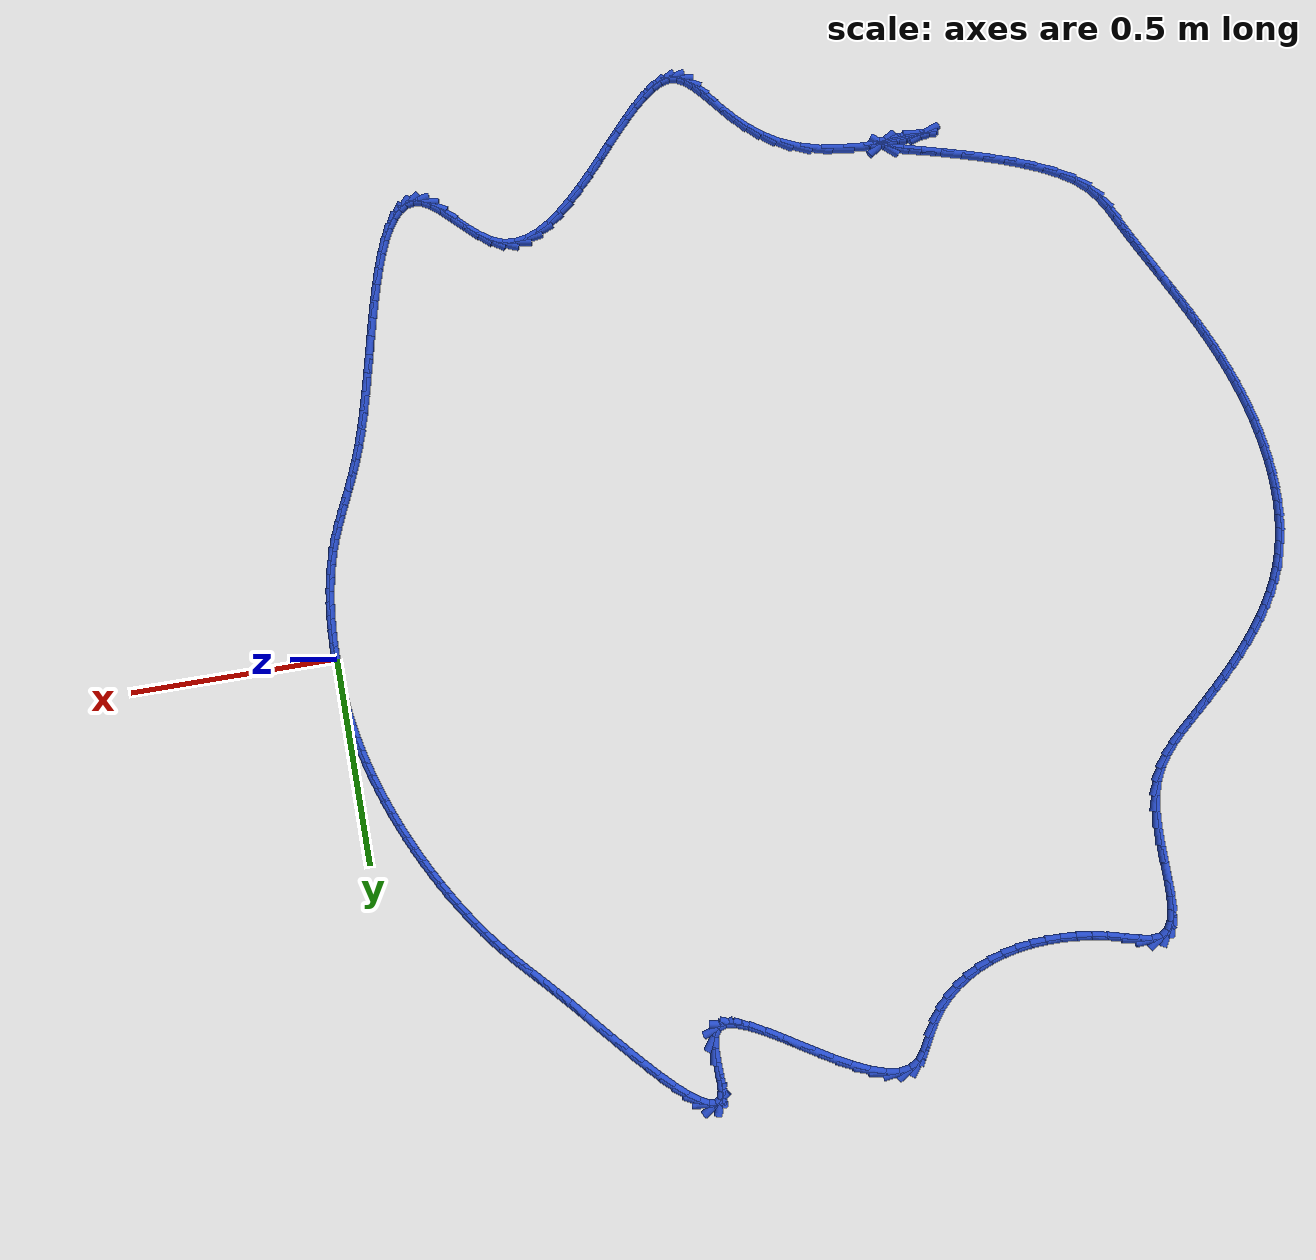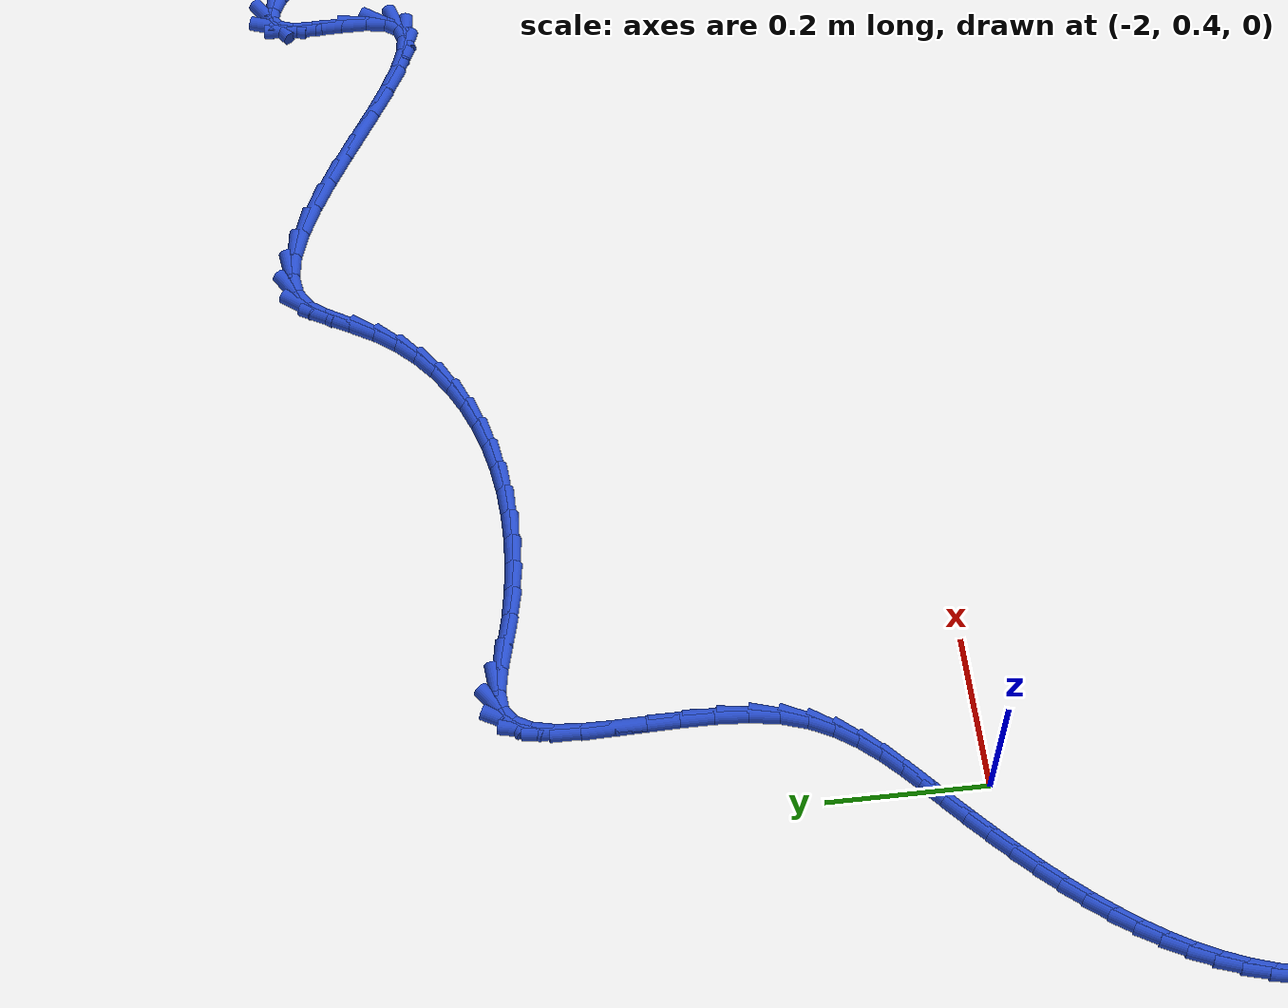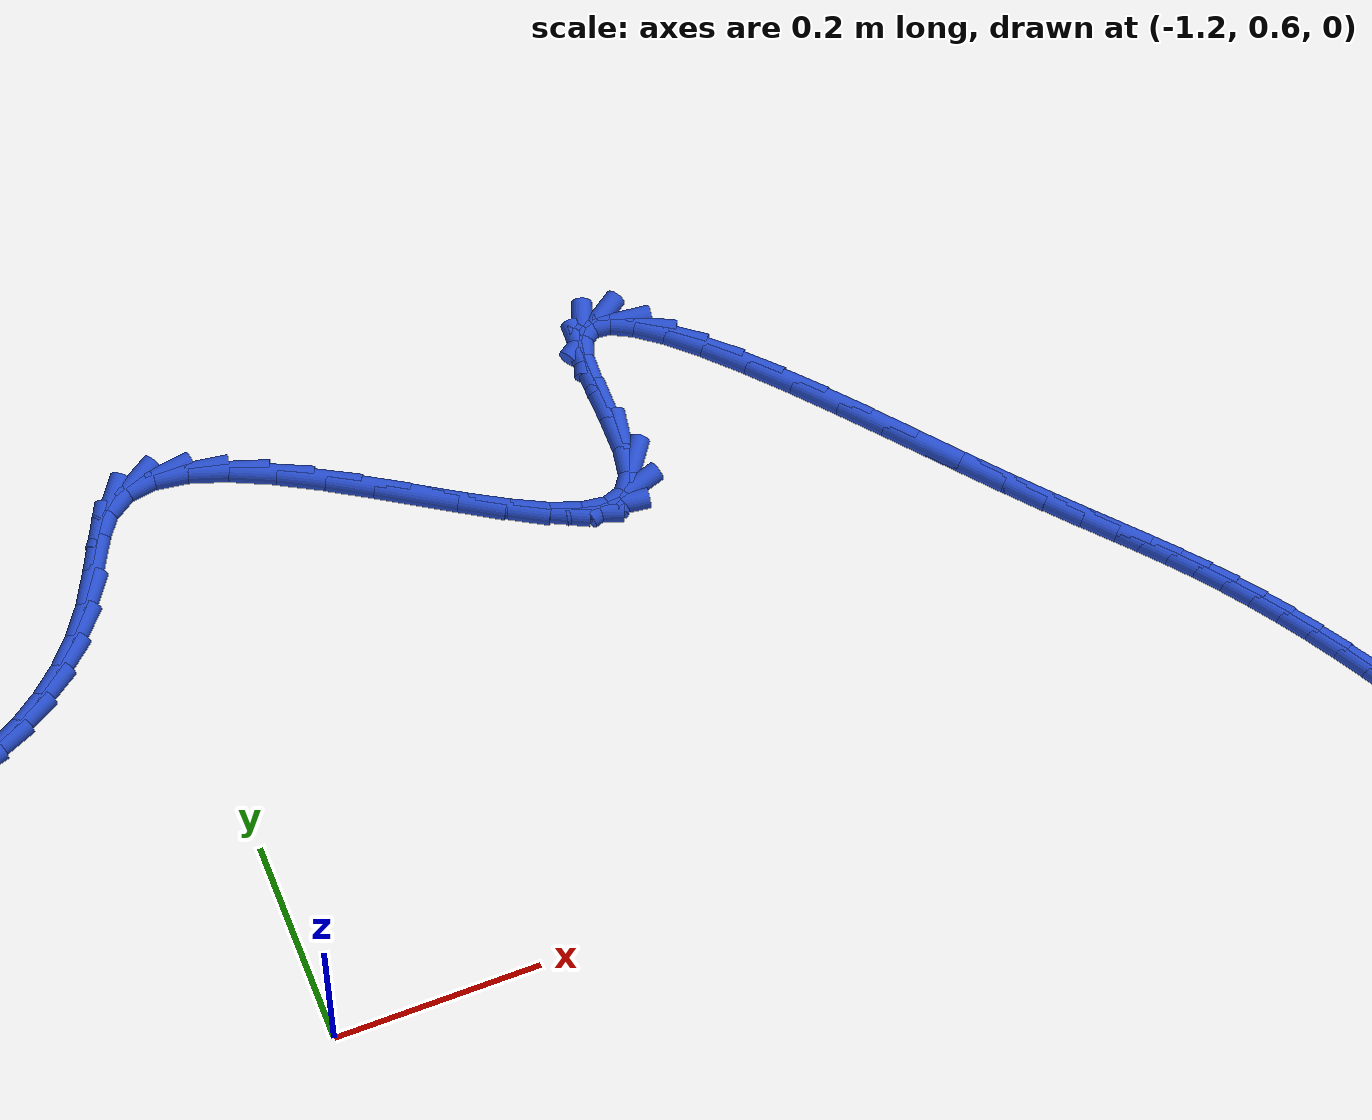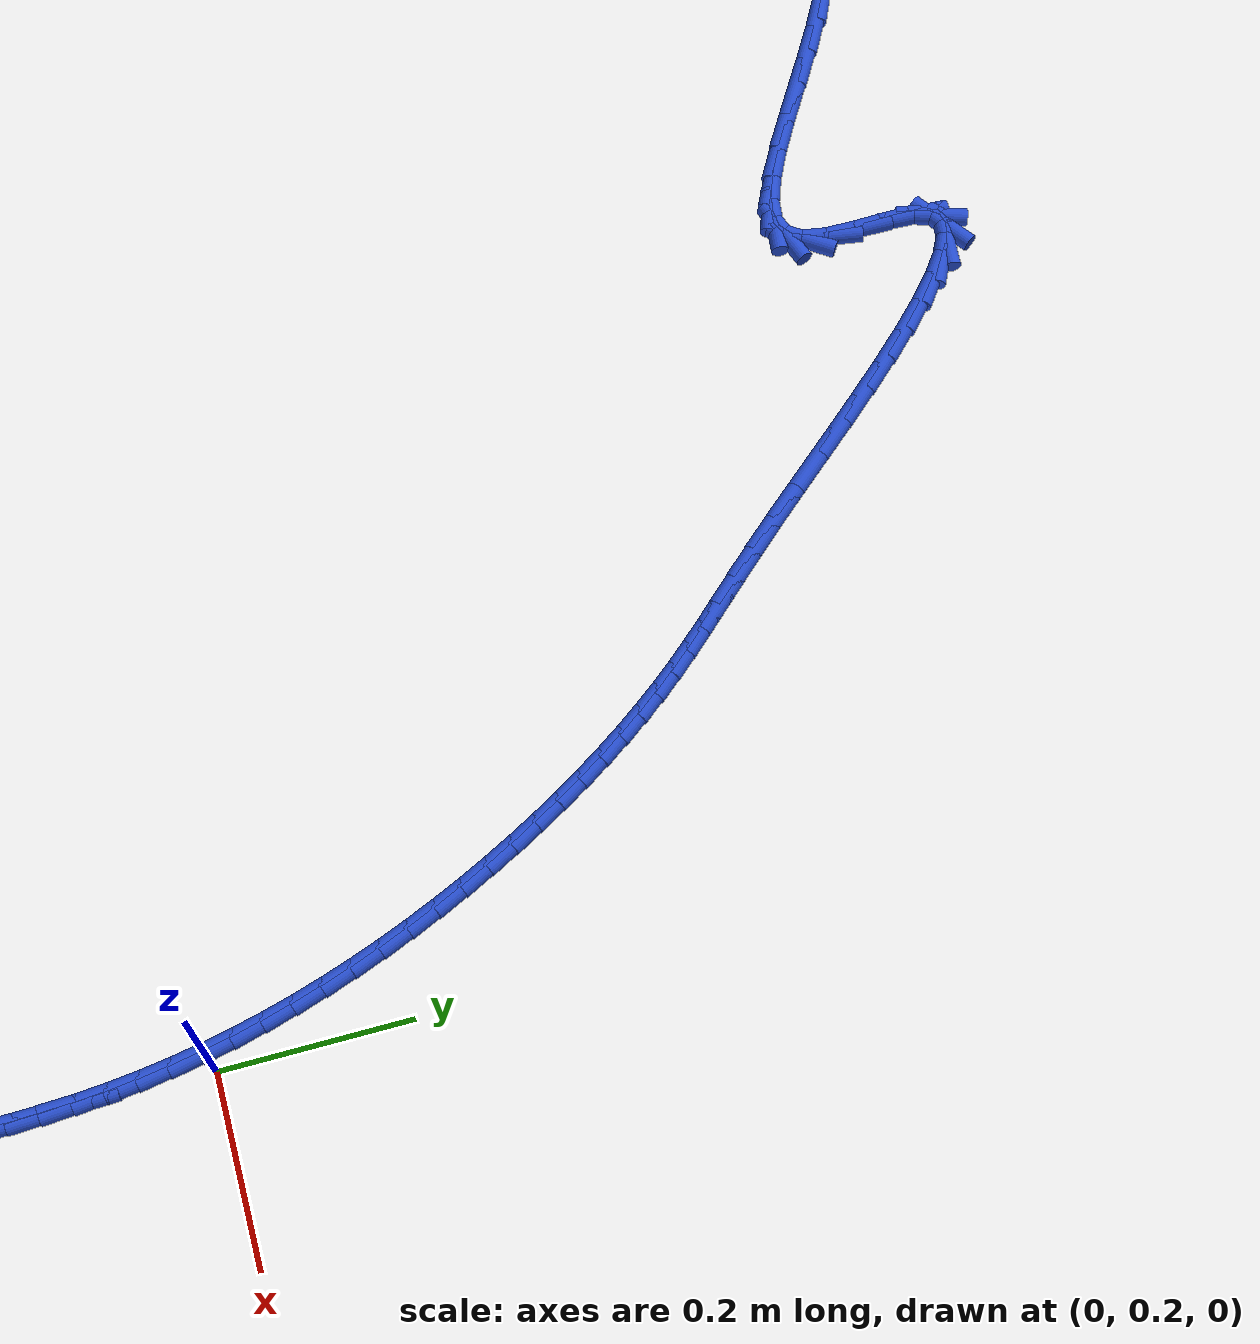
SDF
<sdf version="1.6">
 <world name="default">
  <light name="sun" type="directional">
   <pose>0 0 10 0 -0 0</pose>
   <diffuse>0.8 0.8 0.8 1</diffuse>
   <specular>0.2 0.2 0.2 1</specular>
   <attenuation>
    <range>1000</range>
    <constant>0.9</constant>
    <linear>0.01</linear>
    <quadratic>0.001</quadratic>
   </attenuation>
   <direction>-0.5 0.1 -0.9</direction>
  </light>
  <model name="ground_plane">
   <static>1</static>
   <link name="link">
    <collision name="collision">
     <geometry><plane><normal>0 0 1</normal><size>100 100</size></plane></geometry>
     <surface><friction><ode><mu>100</mu><mu2>50</mu2></ode></friction></surface>
    </collision>
    <visual name="visual">
     <cast_shadows>0</cast_shadows>
     <geometry><plane><normal>0 0 1</normal><size>100 100</size></plane></geometry>
     <material>
      <script><uri>file://media/materials/scripts/gazebo.material</uri><name>Gazebo/WhiteGlow</name></script>
     </material>
    </visual>
   </link>
  </model>
  <gravity>0 0 -9.8</gravity>
  <magnetic_field>6e-06 2.3e-05 -4.2e-05</magnetic_field>
  <atmosphere type="adiabatic"/>
  <physics name="default_physics" default="0" type="ode">
   <max_step_size>0.001</max_step_size>
   <real_time_factor>1</real_time_factor>
   <real_time_update_rate>1000</real_time_update_rate>
  </physics>
  <scene><ambient>0.4 0.4 0.4 1</ambient><background>0.7 0.7 0.7 1</background><shadows>1</shadows></scene>
  <spherical_coordinates>
   <surface_model>EARTH_WGS84</surface_model>
   <latitude_deg>0</latitude_deg>
   <longitude_deg>0</longitude_deg>
   <elevation>0</elevation>
   <heading_deg>0</heading_deg>
  </spherical_coordinates>
  <model name="line">
   <link name="link_0">
    <pose>1.734723475976807e-17 -2.7755575615628914e-17 0.01 0 1.57 -1.548209915083858</pose>
    <collision name="collision">
     <geometry><cylinder><radius>0.01</radius><length>0.08</length></cylinder></geometry>
    </collision>
    <visual name="visual">
     <material>
      <script><name>Gazebo/Blue</name><uri>file://media/materials/scripts/gazebo.material</uri></script>
     </material>
     <geometry><cylinder><radius>0.01</radius><length>0.08</length></cylinder></geometry>
    </visual>
   </link>
   <link name="link_1">
    <pose>-0.0007454547674477216 0.032998955703278 0.01 0 1.57 -1.5181772568839937</pose>
    <collision name="collision">
     <geometry><cylinder><radius>0.01</radius><length>0.08</length></cylinder></geometry>
    </collision>
    <visual name="visual">
     <material>
      <script><name>Gazebo/Blue</name><uri>file://media/materials/scripts/gazebo.material</uri></script>
     </material>
     <geometry><cylinder><radius>0.01</radius><length>0.08</length></cylinder></geometry>
    </visual>
   </link>
   <link name="link_2">
    <pose>-0.0024687261284675457 0.06571866407017606 0.01 0 1.57 -1.487441928179385</pose>
    <collision name="collision">
     <geometry><cylinder><radius>0.01</radius><length>0.08</length></cylinder></geometry>
    </collision>
    <visual name="visual">
     <material>
      <script><name>Gazebo/Blue</name><uri>file://media/materials/scripts/gazebo.material</uri></script>
     </material>
     <geometry><cylinder><radius>0.01</radius><length>0.08</length></cylinder></geometry>
    </visual>
   </link>
   <link name="link_3">
    <pose>-0.005183070146105424 0.09820710820907626 0.01 0 1.57 -1.4561899604984563</pose>
    <collision name="collision">
     <geometry><cylinder><radius>0.01</radius><length>0.08</length></cylinder></geometry>
    </collision>
    <visual name="visual">
     <material>
      <script><name>Gazebo/Blue</name><uri>file://media/materials/scripts/gazebo.material</uri></script>
     </material>
     <geometry><cylinder><radius>0.01</radius><length>0.08</length></cylinder></geometry>
    </visual>
   </link>
   <link name="link_4">
    <pose>-0.008901742883407327 0.1305122712283608 0.01 0 1.57 -1.4246199189748514</pose>
    <collision name="collision">
     <geometry><cylinder><radius>0.01</radius><length>0.08</length></cylinder></geometry>
    </collision>
    <visual name="visual">
     <material>
      <script><name>Gazebo/Blue</name><uri>file://media/materials/scripts/gazebo.material</uri></script>
     </material>
     <geometry><cylinder><radius>0.01</radius><length>0.08</length></cylinder></geometry>
    </visual>
   </link>
   <link name="link_5">
    <pose>-0.013638000403419214 0.16268213623641178 0.01 0 1.57 -1.392937703355989</pose>
    <collision name="collision">
     <geometry><cylinder><radius>0.01</radius><length>0.08</length></cylinder></geometry>
    </collision>
    <visual name="visual">
     <material>
      <script><name>Gazebo/Blue</name><uri>file://media/materials/scripts/gazebo.material</uri></script>
     </material>
     <geometry><cylinder><radius>0.01</radius><length>0.08</length></cylinder></geometry>
    </visual>
   </link>
   <link name="link_6">
    <pose>-0.01940509876918707 0.19476468634161145 0.01 0 1.57 -1.3613508756848165</pose>
    <collision name="collision">
     <geometry><cylinder><radius>0.01</radius><length>0.08</length></cylinder></geometry>
    </collision>
    <visual name="visual">
     <material>
      <script><name>Gazebo/Blue</name><uri>file://media/materials/scripts/gazebo.material</uri></script>
     </material>
     <geometry><cylinder><radius>0.01</radius><length>0.08</length></cylinder></geometry>
    </visual>
   </link>
   <link name="link_7">
    <pose>-0.026216294043756846 0.22680790465234182 0.01 0 1.57 -1.3300628873312692</pose>
    <collision name="collision">
     <geometry><cylinder><radius>0.01</radius><length>0.08</length></cylinder></geometry>
    </collision>
    <visual name="visual">
     <material>
      <script><name>Gazebo/Blue</name><uri>file://media/materials/scripts/gazebo.material</uri></script>
     </material>
     <geometry><cylinder><radius>0.01</radius><length>0.08</length></cylinder></geometry>
    </visual>
   </link>
   <link name="link_8">
    <pose>-0.034084842290151705 0.2588597742769432 0.01 0 1.57 -1.2994251704821995</pose>
    <collision name="collision">
     <geometry><cylinder><radius>0.01</radius><length>0.08</length></cylinder></geometry>
    </collision>
    <visual name="visual">
     <material>
      <script><name>Gazebo/Blue</name><uri>file://media/materials/scripts/gazebo.material</uri></script>
     </material>
     <geometry><cylinder><radius>0.01</radius><length>0.08</length></cylinder></geometry>
    </visual>
   </link>
   <link name="link_9">
    <pose>-0.043012814997350136 0.29094767351307854 0.01 0 1.57 -1.2700925666562424</pose>
    <collision name="collision">
     <geometry><cylinder><radius>0.01</radius><length>0.08</length></cylinder></geometry>
    </collision>
    <visual name="visual">
     <material>
      <script><name>Gazebo/Blue</name><uri>file://media/materials/scripts/gazebo.material</uri></script>
     </material>
     <geometry><cylinder><radius>0.01</radius><length>0.08</length></cylinder></geometry>
    </visual>
   </link>
   <link name="link_10">
    <pose>-0.05295771547616046 0.32301687481604785 0.01 0 1.57 -1.2420315779892712</pose>
    <collision name="collision">
     <geometry><cylinder><radius>0.01</radius><length>0.08</length></cylinder></geometry>
    </collision>
    <visual name="visual">
     <material>
      <script><name>Gazebo/Blue</name><uri>file://media/materials/scripts/gazebo.material</uri></script>
     </material>
     <geometry><cylinder><radius>0.01</radius><length>0.08</length></cylinder></geometry>
    </visual>
   </link>
   <link name="link_11">
    <pose>-0.06386594736075604 0.35499220223294825 0.01 0 1.57 -1.215044222370325</pose>
    <collision name="collision">
     <geometry><cylinder><radius>0.01</radius><length>0.08</length></cylinder></geometry>
    </collision>
    <visual name="visual">
     <material>
      <script><name>Gazebo/Blue</name><uri>file://media/materials/scripts/gazebo.material</uri></script>
     </material>
     <geometry><cylinder><radius>0.01</radius><length>0.08</length></cylinder></geometry>
    </visual>
   </link>
   <link name="link_12">
    <pose>-0.07568391428531034 0.38679847981087706 0.01 0 1.57 -1.1889445340298277</pose>
    <collision name="collision">
     <geometry><cylinder><radius>0.01</radius><length>0.08</length></cylinder></geometry>
    </collision>
    <visual name="visual">
     <material>
      <script><name>Gazebo/Blue</name><uri>file://media/materials/scripts/gazebo.material</uri></script>
     </material>
     <geometry><cylinder><radius>0.01</radius><length>0.08</length></cylinder></geometry>
    </visual>
   </link>
   <link name="link_13">
    <pose>-0.08835801988399669 0.4183605315969315 0.01 0 1.57 -1.1635559600941956</pose>
    <collision name="collision">
     <geometry><cylinder><radius>0.01</radius><length>0.08</length></cylinder></geometry>
    </collision>
    <visual name="visual">
     <material>
      <script><name>Gazebo/Blue</name><uri>file://media/materials/scripts/gazebo.material</uri></script>
     </material>
     <geometry><cylinder><radius>0.01</radius><length>0.08</length></cylinder></geometry>
    </visual>
   </link>
   <link name="link_14">
    <pose>-0.10183466779098857 0.4496031816382087 0.01 0 1.57 -1.1387087010911852</pose>
    <collision name="collision">
     <geometry><cylinder><radius>0.01</radius><length>0.08</length></cylinder></geometry>
    </collision>
    <visual name="visual">
     <material>
      <script><name>Gazebo/Blue</name><uri>file://media/materials/scripts/gazebo.material</uri></script>
     </material>
     <geometry><cylinder><radius>0.01</radius><length>0.08</length></cylinder></geometry>
    </visual>
   </link>
   <link name="link_15">
    <pose>-0.11606026164045935 0.48045125398180594 0.01 0 1.57 -1.114236984238482</pose>
    <collision name="collision">
     <geometry><cylinder><radius>0.01</radius><length>0.08</length></cylinder></geometry>
    </collision>
    <visual name="visual">
     <material>
      <script><name>Gazebo/Blue</name><uri>file://media/materials/scripts/gazebo.material</uri></script>
     </material>
     <geometry><cylinder><radius>0.01</radius><length>0.08</length></cylinder></geometry>
    </visual>
   </link>
   <link name="link_16">
    <pose>-0.13098120506658248 0.5108295726748207 0.01 0 1.57 -1.0899762307672962</pose>
    <collision name="collision">
     <geometry><cylinder><radius>0.01</radius><length>0.08</length></cylinder></geometry>
    </collision>
    <visual name="visual">
     <material>
      <script><name>Gazebo/Blue</name><uri>file://media/materials/scripts/gazebo.material</uri></script>
     </material>
     <geometry><cylinder><radius>0.01</radius><length>0.08</length></cylinder></geometry>
    </visual>
   </link>
   <link name="link_17">
    <pose>-0.14654390170353132 0.5406629617643499 0.01 0 1.57 -1.0657600549144857</pose>
    <collision name="collision">
     <geometry><cylinder><radius>0.01</radius><length>0.08</length></cylinder></geometry>
    </collision>
    <visual name="visual">
     <material>
      <script><name>Gazebo/Blue</name><uri>file://media/materials/scripts/gazebo.material</uri></script>
     </material>
     <geometry><cylinder><radius>0.01</radius><length>0.08</length></cylinder></geometry>
    </visual>
   </link>
   <link name="link_18">
    <pose>-0.16269475518547932 0.5698762452974911 0.01 0 1.57 -1.041417009392174</pose>
    <collision name="collision">
     <geometry><cylinder><radius>0.01</radius><length>0.08</length></cylinder></geometry>
    </collision>
    <visual name="visual">
     <material>
      <script><name>Gazebo/Blue</name><uri>file://media/materials/scripts/gazebo.material</uri></script>
     </material>
     <geometry><cylinder><radius>0.01</radius><length>0.08</length></cylinder></geometry>
    </visual>
   </link>
   <link name="link_19">
    <pose>-0.17938016914659982 0.5983942473213409 0.01 0 1.57 -1.0167669674362978</pose>
    <collision name="collision">
     <geometry><cylinder><radius>0.01</radius><length>0.08</length></cylinder></geometry>
    </collision>
    <visual name="visual">
     <material>
      <script><name>Gazebo/Blue</name><uri>file://media/materials/scripts/gazebo.material</uri></script>
     </material>
     <geometry><cylinder><radius>0.01</radius><length>0.08</length></cylinder></geometry>
    </visual>
   </link>
   <link name="link_20">
    <pose>-0.19654654722106638 0.6261417918829976 0.01 0 1.57 -0.9916170025211835</pose>
    <collision name="collision">
     <geometry><cylinder><radius>0.01</radius><length>0.08</length></cylinder></geometry>
    </collision>
    <visual name="visual">
     <material>
      <script><name>Gazebo/Blue</name><uri>file://media/materials/scripts/gazebo.material</uri></script>
     </material>
     <geometry><cylinder><radius>0.01</radius><length>0.08</length></cylinder></geometry>
    </visual>
   </link>
   <link name="link_21">
    <pose>-0.2141402930430522 0.6530437030295575 0.01 0 1.57 -0.9657565911903</pose>
    <collision name="collision">
     <geometry><cylinder><radius>0.01</radius><length>0.08</length></cylinder></geometry>
    </collision>
    <visual name="visual">
     <material>
      <script><name>Gazebo/Blue</name><uri>file://media/materials/scripts/gazebo.material</uri></script>
     </material>
     <geometry><cylinder><radius>0.01</radius><length>0.08</length></cylinder></geometry>
    </visual>
   </link>
   <link name="link_22">
    <pose>-0.2321078102467309 0.6790248048081182 0.01 0 1.57 -0.9389519199759675</pose>
    <collision name="collision">
     <geometry><cylinder><radius>0.01</radius><length>0.08</length></cylinder></geometry>
    </collision>
    <visual name="visual">
     <material>
      <script><name>Gazebo/Blue</name><uri>file://media/materials/scripts/gazebo.material</uri></script>
     </material>
     <geometry><cylinder><radius>0.01</radius><length>0.08</length></cylinder></geometry>
    </visual>
   </link>
   <link name="link_23">
    <pose>-0.25039550246627573 0.7040099212657769 0.01 0 1.57 -0.9109390222016234</pose>
    <collision name="collision">
     <geometry><cylinder><radius>0.01</radius><length>0.08</length></cylinder></geometry>
    </collision>
    <visual name="visual">
     <material>
      <script><name>Gazebo/Blue</name><uri>file://media/materials/scripts/gazebo.material</uri></script>
     </material>
     <geometry><cylinder><radius>0.01</radius><length>0.08</length></cylinder></geometry>
    </visual>
   </link>
   <link name="link_24">
    <pose>-0.26894977333586023 0.727923876449631 0.01 0 1.57 -0.8814668753098024</pose>
    <collision name="collision">
     <geometry><cylinder><radius>0.01</radius><length>0.08</length></cylinder></geometry>
    </collision>
    <visual name="visual">
     <material>
      <script><name>Gazebo/Blue</name><uri>file://media/materials/scripts/gazebo.material</uri></script>
     </material>
     <geometry><cylinder><radius>0.01</radius><length>0.08</length></cylinder></geometry>
    </visual>
   </link>
   <link name="link_25">
    <pose>-0.2877200092066353 0.7506975010942152 0.01 0 1.57 -0.8533691286584695</pose>
    <collision name="collision">
     <geometry><cylinder><radius>0.01</radius><length>0.08</length></cylinder></geometry>
    </collision>
    <visual name="visual">
     <material>
      <script><name>Gazebo/Blue</name><uri>file://media/materials/scripts/gazebo.material</uri></script>
     </material>
     <geometry><cylinder><radius>0.01</radius><length>0.08</length></cylinder></geometry>
    </visual>
   </link>
   <link name="link_26">
    <pose>-0.30681451839543594 0.7725816678897727 0.01 0 1.57 -0.8325446957663478</pose>
    <collision name="collision">
     <geometry><cylinder><radius>0.01</radius><length>0.08</length></cylinder></geometry>
    </collision>
    <visual name="visual">
     <material>
      <script><name>Gazebo/Blue</name><uri>file://media/materials/scripts/gazebo.material</uri></script>
     </material>
     <geometry><cylinder><radius>0.01</radius><length>0.08</length></cylinder></geometry>
    </visual>
   </link>
   <link name="link_27">
    <pose>-0.32657705771119194 0.7943014029612485 0.01 0 1.57 -0.8207633309209007</pose>
    <collision name="collision">
     <geometry><cylinder><radius>0.01</radius><length>0.08</length></cylinder></geometry>
    </collision>
    <visual name="visual">
     <material>
      <script><name>Gazebo/Blue</name><uri>file://media/materials/scripts/gazebo.material</uri></script>
     </material>
     <geometry><cylinder><radius>0.01</radius><length>0.08</length></cylinder></geometry>
    </visual>
   </link>
   <link name="link_28">
    <pose>-0.34737041720812895 0.8166200621699572 0.01 0 1.57 -0.8179577794529534</pose>
    <collision name="collision">
     <geometry><cylinder><radius>0.01</radius><length>0.08</length></cylinder></geometry>
    </collision>
    <visual name="visual">
     <material>
      <script><name>Gazebo/Blue</name><uri>file://media/materials/scripts/gazebo.material</uri></script>
     </material>
     <geometry><cylinder><radius>0.01</radius><length>0.08</length></cylinder></geometry>
    </visual>
   </link>
   <link name="link_29">
    <pose>-0.36955738694047285 0.8403010013772138 0.01 0 1.57 -0.8228320672777447</pose>
    <collision name="collision">
     <geometry><cylinder><radius>0.01</radius><length>0.08</length></cylinder></geometry>
    </collision>
    <visual name="visual">
     <material>
      <script><name>Gazebo/Blue</name><uri>file://media/materials/scripts/gazebo.material</uri></script>
     </material>
     <geometry><cylinder><radius>0.01</radius><length>0.08</length></cylinder></geometry>
    </visual>
   </link>
   <link name="link_30">
    <pose>-0.3935007569624495 0.8661075764443324 0.01 0 1.57 -0.8334454599610085</pose>
    <collision name="collision">
     <geometry><cylinder><radius>0.01</radius><length>0.08</length></cylinder></geometry>
    </collision>
    <visual name="visual">
     <material>
      <script><name>Gazebo/Blue</name><uri>file://media/materials/scripts/gazebo.material</uri></script>
     </material>
     <geometry><cylinder><radius>0.01</radius><length>0.08</length></cylinder></geometry>
    </visual>
   </link>
   <link name="link_31">
    <pose>-0.41956331732828483 0.8948031432326289 0.01 0 1.57 -0.8466433084690395</pose>
    <collision name="collision">
     <geometry><cylinder><radius>0.01</radius><length>0.08</length></cylinder></geometry>
    </collision>
    <visual name="visual">
     <material>
      <script><name>Gazebo/Blue</name><uri>file://media/materials/scripts/gazebo.material</uri></script>
     </material>
     <geometry><cylinder><radius>0.01</radius><length>0.08</length></cylinder></geometry>
    </visual>
   </link>
   <link name="link_32">
    <pose>-0.44801624077959057 0.9269736039240537 0.01 0 1.57 -0.8539610731692683</pose>
    <collision name="collision">
     <geometry><cylinder><radius>0.01</radius><length>0.08</length></cylinder></geometry>
    </collision>
    <visual name="visual">
     <material>
      <script><name>Gazebo/Blue</name><uri>file://media/materials/scripts/gazebo.material</uri></script>
     </material>
     <geometry><cylinder><radius>0.01</radius><length>0.08</length></cylinder></geometry>
    </visual>
   </link>
   <link name="link_33">
    <pose>-0.47846133768090254 0.961908371933856 0.01 0 1.57 -0.8538279165964507</pose>
    <collision name="collision">
     <geometry><cylinder><radius>0.01</radius><length>0.08</length></cylinder></geometry>
    </collision>
    <visual name="visual">
     <material>
      <script><name>Gazebo/Blue</name><uri>file://media/materials/scripts/gazebo.material</uri></script>
     </material>
     <geometry><cylinder><radius>0.01</radius><length>0.08</length></cylinder></geometry>
    </visual>
   </link>
   <link name="link_34">
    <pose>-0.5102034129683446 0.9983215905175425 0.01 0 1.57 -0.8471175512862784</pose>
    <collision name="collision">
     <geometry><cylinder><radius>0.01</radius><length>0.08</length></cylinder></geometry>
    </collision>
    <visual name="visual">
     <material>
      <script><name>Gazebo/Blue</name><uri>file://media/materials/scripts/gazebo.material</uri></script>
     </material>
     <geometry><cylinder><radius>0.01</radius><length>0.08</length></cylinder></geometry>
    </visual>
   </link>
   <link name="link_35">
    <pose>-0.5425459338104048 1.0349248118069303 0.01 0 1.57 -0.8334538950789813</pose>
    <collision name="collision">
     <geometry><cylinder><radius>0.01</radius><length>0.08</length></cylinder></geometry>
    </collision>
    <visual name="visual">
     <material>
      <script><name>Gazebo/Blue</name><uri>file://media/materials/scripts/gazebo.material</uri></script>
     </material>
     <geometry><cylinder><radius>0.01</radius><length>0.08</length></cylinder></geometry>
    </visual>
   </link>
   <link name="link_36">
    <pose>-0.5747923673755702 1.070429587933834 0.01 0 1.57 -0.8111633435640325</pose>
    <collision name="collision">
     <geometry><cylinder><radius>0.01</radius><length>0.08</length></cylinder></geometry>
    </collision>
    <visual name="visual">
     <material>
      <script><name>Gazebo/Blue</name><uri>file://media/materials/scripts/gazebo.material</uri></script>
     </material>
     <geometry><cylinder><radius>0.01</radius><length>0.08</length></cylinder></geometry>
    </visual>
   </link>
   <link name="link_37">
    <pose>-0.6062461808323287 1.1035474710300708 0.01 0 1.57 -0.7766095846918781</pose>
    <collision name="collision">
     <geometry><cylinder><radius>0.01</radius><length>0.08</length></cylinder></geometry>
    </collision>
    <visual name="visual">
     <material>
      <script><name>Gazebo/Blue</name><uri>file://media/materials/scripts/gazebo.material</uri></script>
     </material>
     <geometry><cylinder><radius>0.01</radius><length>0.08</length></cylinder></geometry>
    </visual>
   </link>
   <link name="link_38">
    <pose>-0.6362108413491675 1.1329900132274562 0.01 0 1.57 -0.7223291303064018</pose>
    <collision name="collision">
     <geometry><cylinder><radius>0.01</radius><length>0.08</length></cylinder></geometry>
    </collision>
    <visual name="visual">
     <material>
      <script><name>Gazebo/Blue</name><uri>file://media/materials/scripts/gazebo.material</uri></script>
     </material>
     <geometry><cylinder><radius>0.01</radius><length>0.08</length></cylinder></geometry>
    </visual>
   </link>
   <link name="link_39">
    <pose>-0.6639898160945746 1.1574687666578067 0.01 0 1.57 -0.6319359223688805</pose>
    <collision name="collision">
     <geometry><cylinder><radius>0.01</radius><length>0.08</length></cylinder></geometry>
    </collision>
    <visual name="visual">
     <material>
      <script><name>Gazebo/Blue</name><uri>file://media/materials/scripts/gazebo.material</uri></script>
     </material>
     <geometry><cylinder><radius>0.01</radius><length>0.08</length></cylinder></geometry>
    </visual>
   </link>
   <link name="link_40">
    <pose>-0.6888865722370374 1.175695283452938 0.01 0 1.57 -0.46465394815971384</pose>
    <collision name="collision">
     <geometry><cylinder><radius>0.01</radius><length>0.08</length></cylinder></geometry>
    </collision>
    <visual name="visual">
     <material>
      <script><name>Gazebo/Blue</name><uri>file://media/materials/scripts/gazebo.material</uri></script>
     </material>
     <geometry><cylinder><radius>0.01</radius><length>0.08</length></cylinder></geometry>
    </visual>
   </link>
   <link name="link_41">
    <pose>-0.7102045769450434 1.1863811157446658 0.01 0 1.57 -0.10851590374548921</pose>
    <collision name="collision">
     <geometry><cylinder><radius>0.01</radius><length>0.08</length></cylinder></geometry>
    </collision>
    <visual name="visual">
     <material>
      <script><name>Gazebo/Blue</name><uri>file://media/materials/scripts/gazebo.material</uri></script>
     </material>
     <geometry><cylinder><radius>0.01</radius><length>0.08</length></cylinder></geometry>
    </visual>
   </link>
   <link name="link_42">
    <pose>-0.72724729738708 1.188237815664807 0.01 0 1.57 0.6001540998965172</pose>
    <collision name="collision">
     <geometry><cylinder><radius>0.01</radius><length>0.08</length></cylinder></geometry>
    </collision>
    <visual name="visual">
     <material>
      <script><name>Gazebo/Blue</name><uri>file://media/materials/scripts/gazebo.material</uri></script>
     </material>
     <geometry><cylinder><radius>0.01</radius><length>0.08</length></cylinder></geometry>
    </visual>
   </link>
   <link name="link_43">
    <pose>-0.7393182007316359 1.1799769353451777 0.01 0 1.57 1.2559865538017163</pose>
    <collision name="collision">
     <geometry><cylinder><radius>0.01</radius><length>0.08</length></cylinder></geometry>
    </collision>
    <visual name="visual">
     <material>
      <script><name>Gazebo/Blue</name><uri>file://media/materials/scripts/gazebo.material</uri></script>
     </material>
     <geometry><cylinder><radius>0.01</radius><length>0.08</length></cylinder></geometry>
    </visual>
   </link>
   <link name="link_44">
    <pose>-0.7457218643800103 1.160312021067337 0.01 0 1.57 1.537572953300119</pose>
    <collision name="collision">
     <geometry><cylinder><radius>0.01</radius><length>0.08</length></cylinder></geometry>
    </collision>
    <visual name="visual">
     <material>
      <script><name>Gazebo/Blue</name><uri>file://media/materials/scripts/gazebo.material</uri></script>
     </material>
     <geometry><cylinder><radius>0.01</radius><length>0.08</length></cylinder></geometry>
    </visual>
   </link>
   <link name="link_45">
    <pose>-0.7467389472333037 1.1297098123615996 0.01 0 1.57 -1.5341523114455065</pose>
    <collision name="collision">
     <geometry><cylinder><radius>0.01</radius><length>0.08</length></cylinder></geometry>
    </collision>
    <visual name="visual">
     <material>
      <script><name>Gazebo/Blue</name><uri>file://media/materials/scripts/gazebo.material</uri></script>
     </material>
     <geometry><cylinder><radius>0.01</radius><length>0.08</length></cylinder></geometry>
    </visual>
   </link>
   <link name="link_46">
    <pose>-0.7454152828755848 1.0936037299081738 0.01 0 1.57 -1.5670487115709915</pose>
    <collision name="collision">
     <geometry><cylinder><radius>0.01</radius><length>0.08</length></cylinder></geometry>
    </collision>
    <visual name="visual">
     <material>
      <script><name>Gazebo/Blue</name><uri>file://media/materials/scripts/gazebo.material</uri></script>
     </material>
     <geometry><cylinder><radius>0.01</radius><length>0.08</length></cylinder></geometry>
    </visual>
   </link>
   <link name="link_47">
    <pose>-0.7452829797812667 1.05830061925493 0.01 0 1.57 1.4094347121905135</pose>
    <collision name="collision">
     <geometry><cylinder><radius>0.01</radius><length>0.08</length></cylinder></geometry>
    </collision>
    <visual name="visual">
     <material>
      <script><name>Gazebo/Blue</name><uri>file://media/materials/scripts/gazebo.material</uri></script>
     </material>
     <geometry><cylinder><radius>0.01</radius><length>0.08</length></cylinder></geometry>
    </visual>
   </link>
   <link name="link_48">
    <pose>-0.749872634406647 1.0301046270863108 0.01 0 1.57 0.9552593737708631</pose>
    <collision name="collision">
     <geometry><cylinder><radius>0.01</radius><length>0.08</length></cylinder></geometry>
    </collision>
    <visual name="visual">
     <material>
      <script><name>Gazebo/Blue</name><uri>file://media/materials/scripts/gazebo.material</uri></script>
     </material>
     <geometry><cylinder><radius>0.01</radius><length>0.08</length></cylinder></geometry>
    </visual>
   </link>
   <link name="link_49">
    <pose>-0.761659916201311 1.0134369174109057 0.01 0 1.57 0.3074430345813861</pose>
    <collision name="collision">
     <geometry><cylinder><radius>0.01</radius><length>0.08</length></cylinder></geometry>
    </collision>
    <visual name="visual">
     <material>
      <script><name>Gazebo/Blue</name><uri>file://media/materials/scripts/gazebo.material</uri></script>
     </material>
     <geometry><cylinder><radius>0.01</radius><length>0.08</length></cylinder></geometry>
    </visual>
   </link>
   <link name="link_50">
    <pose>-0.7802211674715076 1.007543525770775 0.01 0 1.57 -0.13214751877878148</pose>
    <collision name="collision">
     <geometry><cylinder><radius>0.01</radius><length>0.08</length></cylinder></geometry>
    </collision>
    <visual name="visual">
     <material>
      <script><name>Gazebo/Blue</name><uri>file://media/materials/scripts/gazebo.material</uri></script>
     </material>
     <geometry><cylinder><radius>0.01</radius><length>0.08</length></cylinder></geometry>
    </visual>
   </link>
   <link name="link_51">
    <pose>-0.8046389933685395 1.0107891959188111 0.01 0 1.57 -0.3510015388121623</pose>
    <collision name="collision">
     <geometry><cylinder><radius>0.01</radius><length>0.08</length></cylinder></geometry>
    </collision>
    <visual name="visual">
     <material>
      <script><name>Gazebo/Blue</name><uri>file://media/materials/scripts/gazebo.material</uri></script>
     </material>
     <geometry><cylinder><radius>0.01</radius><length>0.08</length></cylinder></geometry>
    </visual>
   </link>
   <link name="link_52">
    <pose>-0.8339959990437096 1.0215386716079062 0.01 0 1.57 -0.46193559147457736</pose>
    <collision name="collision">
     <geometry><cylinder><radius>0.01</radius><length>0.08</length></cylinder></geometry>
    </collision>
    <visual name="visual">
     <material>
      <script><name>Gazebo/Blue</name><uri>file://media/materials/scripts/gazebo.material</uri></script>
     </material>
     <geometry><cylinder><radius>0.01</radius><length>0.08</length></cylinder></geometry>
    </visual>
   </link>
   <link name="link_53">
    <pose>-0.8673747896483212 1.0381566965909526 0.01 0 1.57 -0.5192243445969936</pose>
    <collision name="collision">
     <geometry><cylinder><radius>0.01</radius><length>0.08</length></cylinder></geometry>
    </collision>
    <visual name="visual">
     <material>
      <script><name>Gazebo/Blue</name><uri>file://media/materials/scripts/gazebo.material</uri></script>
     </material>
     <geometry><cylinder><radius>0.01</radius><length>0.08</length></cylinder></geometry>
    </visual>
   </link>
   <link name="link_54">
    <pose>-0.9038579703336772 1.059008014620842 0.01 0 1.57 -0.5451075635600278</pose>
    <collision name="collision">
     <geometry><cylinder><radius>0.01</radius><length>0.08</length></cylinder></geometry>
    </collision>
    <visual name="visual">
     <material>
      <script><name>Gazebo/Blue</name><uri>file://media/materials/scripts/gazebo.material</uri></script>
     </material>
     <geometry><cylinder><radius>0.01</radius><length>0.08</length></cylinder></geometry>
    </visual>
   </link>
   <link name="link_55">
    <pose>-0.9425281462510804 1.082457369450467 0.01 0 1.57 -0.5486313282352184</pose>
    <collision name="collision">
     <geometry><cylinder><radius>0.01</radius><length>0.08</length></cylinder></geometry>
    </collision>
    <visual name="visual">
     <material>
      <script><name>Gazebo/Blue</name><uri>file://media/materials/scripts/gazebo.material</uri></script>
     </material>
     <geometry><cylinder><radius>0.01</radius><length>0.08</length></cylinder></geometry>
    </visual>
   </link>
   <link name="link_56">
    <pose>-0.9824679225518341 1.1068695048327193 0.01 0 1.57 -0.5324335473141705</pose>
    <collision name="collision">
     <geometry><cylinder><radius>0.01</radius><length>0.08</length></cylinder></geometry>
    </collision>
    <visual name="visual">
     <material>
      <script><name>Gazebo/Blue</name><uri>file://media/materials/scripts/gazebo.material</uri></script>
     </material>
     <geometry><cylinder><radius>0.01</radius><length>0.08</length></cylinder></geometry>
    </visual>
   </link>
   <link name="link_57">
    <pose>-1.0227599043872415 1.1306091645204914 0.01 0 1.57 -0.4947328696898481</pose>
    <collision name="collision">
     <geometry><cylinder><radius>0.01</radius><length>0.08</length></cylinder></geometry>
    </collision>
    <visual name="visual">
     <material>
      <script><name>Gazebo/Blue</name><uri>file://media/materials/scripts/gazebo.material</uri></script>
     </material>
     <geometry><cylinder><radius>0.01</radius><length>0.08</length></cylinder></geometry>
    </visual>
   </link>
   <link name="link_58">
    <pose>-1.062486696908605 1.1520410922666753 0.01 0 1.57 -0.4289050384086867</pose>
    <collision name="collision">
     <geometry><cylinder><radius>0.01</radius><length>0.08</length></cylinder></geometry>
    </collision>
    <visual name="visual">
     <material>
      <script><name>Gazebo/Blue</name><uri>file://media/materials/scripts/gazebo.material</uri></script>
     </material>
     <geometry><cylinder><radius>0.01</radius><length>0.08</length></cylinder></geometry>
    </visual>
   </link>
   <link name="link_59">
    <pose>-1.1007309052672283 1.169530031824163 0.01 0 1.57 -0.32081166647994497</pose>
    <collision name="collision">
     <geometry><cylinder><radius>0.01</radius><length>0.08</length></cylinder></geometry>
    </collision>
    <visual name="visual">
     <material>
      <script><name>Gazebo/Blue</name><uri>file://media/materials/scripts/gazebo.material</uri></script>
     </material>
     <geometry><cylinder><radius>0.01</radius><length>0.08</length></cylinder></geometry>
    </visual>
   </link>
   <link name="link_60">
    <pose>-1.136575134614414 1.1814407269458471 0.01 0 1.57 -0.14341825878485148</pose>
    <collision name="collision">
     <geometry><cylinder><radius>0.01</radius><length>0.08</length></cylinder></geometry>
    </collision>
    <visual name="visual">
     <material>
      <script><name>Gazebo/Blue</name><uri>file://media/materials/scripts/gazebo.material</uri></script>
     </material>
     <geometry><cylinder><radius>0.01</radius><length>0.08</length></cylinder></geometry>
    </visual>
   </link>
   <link name="link_61">
    <pose>-1.1691019901014656 1.1861379213846197 0.01 0 1.57 0.14569953491411228</pose>
    <collision name="collision">
     <geometry><cylinder><radius>0.01</radius><length>0.08</length></cylinder></geometry>
    </collision>
    <visual name="visual">
     <material>
      <script><name>Gazebo/Blue</name><uri>file://media/materials/scripts/gazebo.material</uri></script>
     </material>
     <geometry><cylinder><radius>0.01</radius><length>0.08</length></cylinder></geometry>
    </visual>
   </link>
   <link name="link_62">
    <pose>-1.1973940768796858 1.1819863588933726 0.01 0 1.57 0.5636500221404637</pose>
    <collision name="collision">
     <geometry><cylinder><radius>0.01</radius><length>0.08</length></cylinder></geometry>
    </collision>
    <visual name="visual">
     <material>
      <script><name>Gazebo/Blue</name><uri>file://media/materials/scripts/gazebo.material</uri></script>
     </material>
     <geometry><cylinder><radius>0.01</radius><length>0.08</length></cylinder></geometry>
    </visual>
   </link>
   <link name="link_63">
    <pose>-1.2205383273197519 1.1673581293471802 0.01 0 1.57 0.9375242739846468</pose>
    <collision name="collision">
     <geometry><cylinder><radius>0.01</radius><length>0.08</length></cylinder></geometry>
    </collision>
    <visual name="visual">
     <material>
      <script><name>Gazebo/Blue</name><uri>file://media/materials/scripts/gazebo.material</uri></script>
     </material>
     <geometry><cylinder><radius>0.01</radius><length>0.08</length></cylinder></geometry>
    </visual>
   </link>
   <link name="link_64">
    <pose>-1.238753407983604 1.1425466159339859 0.01 0 1.57 1.0801588958837494</pose>
    <collision name="collision">
     <geometry><cylinder><radius>0.01</radius><length>0.08</length></cylinder></geometry>
    </collision>
    <visual name="visual">
     <material>
      <script><name>Gazebo/Blue</name><uri>file://media/materials/scripts/gazebo.material</uri></script>
     </material>
     <geometry><cylinder><radius>0.01</radius><length>0.08</length></cylinder></geometry>
    </visual>
   </link>
   <link name="link_65">
    <pose>-1.2548974371059798 1.1123260780825786 0.01 0 1.57 1.0526980294535568</pose>
    <collision name="collision">
     <geometry><cylinder><radius>0.01</radius><length>0.08</length></cylinder></geometry>
    </collision>
    <visual name="visual">
     <material>
      <script><name>Gazebo/Blue</name><uri>file://media/materials/scripts/gazebo.material</uri></script>
     </material>
     <geometry><cylinder><radius>0.01</radius><length>0.08</length></cylinder></geometry>
    </visual>
   </link>
   <link name="link_66">
    <pose>-1.2721612819006145 1.0820407266860472 0.01 0 1.57 0.9372776419822589</pose>
    <collision name="collision">
     <geometry><cylinder><radius>0.01</radius><length>0.08</length></cylinder></geometry>
    </collision>
    <visual name="visual">
     <material>
      <script><name>Gazebo/Blue</name><uri>file://media/materials/scripts/gazebo.material</uri></script>
     </material>
     <geometry><cylinder><radius>0.01</radius><length>0.08</length></cylinder></geometry>
    </visual>
   </link>
   <link name="link_67">
    <pose>-1.2922511116314963 1.0546896834798576 0.01 0 1.57 0.8176120668281966</pose>
    <collision name="collision">
     <geometry><cylinder><radius>0.01</radius><length>0.08</length></cylinder></geometry>
    </collision>
    <visual name="visual">
     <material>
      <script><name>Gazebo/Blue</name><uri>file://media/materials/scripts/gazebo.material</uri></script>
     </material>
     <geometry><cylinder><radius>0.01</radius><length>0.08</length></cylinder></geometry>
    </visual>
   </link>
   <link name="link_68">
    <pose>-1.3150424403924694 1.0303805395742782 0.01 0 1.57 0.7015213070041155</pose>
    <collision name="collision">
     <geometry><cylinder><radius>0.01</radius><length>0.08</length></cylinder></geometry>
    </collision>
    <visual name="visual">
     <material>
      <script><name>Gazebo/Blue</name><uri>file://media/materials/scripts/gazebo.material</uri></script>
     </material>
     <geometry><cylinder><radius>0.01</radius><length>0.08</length></cylinder></geometry>
    </visual>
   </link>
   <link name="link_69">
    <pose>-1.3402978207778222 1.0090424627256023 0.01 0 1.57 0.5909321300325567</pose>
    <collision name="collision">
     <geometry><cylinder><radius>0.01</radius><length>0.08</length></cylinder></geometry>
    </collision>
    <visual name="visual">
     <material>
      <script><name>Gazebo/Blue</name><uri>file://media/materials/scripts/gazebo.material</uri></script>
     </material>
     <geometry><cylinder><radius>0.01</radius><length>0.08</length></cylinder></geometry>
    </visual>
   </link>
   <link name="link_70">
    <pose>-1.3677798053818442 0.9906046206901238 0.01 0 1.57 0.4870601055811412</pose>
    <collision name="collision">
     <geometry><cylinder><radius>0.01</radius><length>0.08</length></cylinder></geometry>
    </collision>
    <visual name="visual">
     <material>
      <script><name>Gazebo/Blue</name><uri>file://media/materials/scripts/gazebo.material</uri></script>
     </material>
     <geometry><cylinder><radius>0.01</radius><length>0.08</length></cylinder></geometry>
    </visual>
   </link>
   <link name="link_71">
    <pose>-1.3972509467988241 0.974996181224137 0.01 0 1.57 0.39042632257762094</pose>
    <collision name="collision">
     <geometry><cylinder><radius>0.01</radius><length>0.08</length></cylinder></geometry>
    </collision>
    <visual name="visual">
     <material>
      <script><name>Gazebo/Blue</name><uri>file://media/materials/scripts/gazebo.material</uri></script>
     </material>
     <geometry><cylinder><radius>0.01</radius><length>0.08</length></cylinder></geometry>
    </visual>
   </link>
   <link name="link_72">
    <pose>-1.428473797623051 0.9621463120839354 0.01 0 1.57 0.30098536017209043</pose>
    <collision name="collision">
     <geometry><cylinder><radius>0.01</radius><length>0.08</length></cylinder></geometry>
    </collision>
    <visual name="visual">
     <material>
      <script><name>Gazebo/Blue</name><uri>file://media/materials/scripts/gazebo.material</uri></script>
     </material>
     <geometry><cylinder><radius>0.01</radius><length>0.08</length></cylinder></geometry>
    </visual>
   </link>
   <link name="link_73">
    <pose>-1.4612109104488142 0.951984181025813 0.01 0 1.57 0.21829278797396418</pose>
    <collision name="collision">
     <geometry><cylinder><radius>0.01</radius><length>0.08</length></cylinder></geometry>
    </collision>
    <visual name="visual">
     <material>
      <script><name>Gazebo/Blue</name><uri>file://media/materials/scripts/gazebo.material</uri></script>
     </material>
     <geometry><cylinder><radius>0.01</radius><length>0.08</length></cylinder></geometry>
    </visual>
   </link>
   <link name="link_74">
    <pose>-1.4952248378704032 0.9444389558060627 0.01 0 1.57 0.14166047389862013</pose>
    <collision name="collision">
     <geometry><cylinder><radius>0.01</radius><length>0.08</length></cylinder></geometry>
    </collision>
    <visual name="visual">
     <material>
      <script><name>Gazebo/Blue</name><uri>file://media/materials/scripts/gazebo.material</uri></script>
     </material>
     <geometry><cylinder><radius>0.01</radius><length>0.08</length></cylinder></geometry>
    </visual>
   </link>
   <link name="link_75">
    <pose>-1.5302781324821064 0.9394398041809794 0.01 0 1.57 0.07027580262535414</pose>
    <collision name="collision">
     <geometry><cylinder><radius>0.01</radius><length>0.08</length></cylinder></geometry>
    </collision>
    <visual name="visual">
     <material>
      <script><name>Gazebo/Blue</name><uri>file://media/materials/scripts/gazebo.material</uri></script>
     </material>
     <geometry><cylinder><radius>0.01</radius><length>0.08</length></cylinder></geometry>
    </visual>
   </link>
   <link name="link_76">
    <pose>-1.5661333468782126 0.936915893906856 0.01 0 1.57 0.0032812126788304657</pose>
    <collision name="collision">
     <geometry><cylinder><radius>0.01</radius><length>0.08</length></cylinder></geometry>
    </collision>
    <visual name="visual">
     <material>
      <script><name>Gazebo/Blue</name><uri>file://media/materials/scripts/gazebo.material</uri></script>
     </material>
     <geometry><cylinder><radius>0.01</radius><length>0.08</length></cylinder></geometry>
    </visual>
   </link>
   <link name="link_77">
    <pose>-1.6025530336530118 0.9367963927399872 0.01 0 1.57 -0.06017959501228952</pose>
    <collision name="collision">
     <geometry><cylinder><radius>0.01</radius><length>0.08</length></cylinder></geometry>
    </collision>
    <visual name="visual">
     <material>
      <script><name>Gazebo/Blue</name><uri>file://media/materials/scripts/gazebo.material</uri></script>
     </material>
     <geometry><cylinder><radius>0.01</radius><length>0.08</length></cylinder></geometry>
    </visual>
   </link>
   <link name="link_78">
    <pose>-1.6392997454007927 0.939010468436666 0.01 0 1.57 -0.12093977044117313</pose>
    <collision name="collision">
     <geometry><cylinder><radius>0.01</radius><length>0.08</length></cylinder></geometry>
    </collision>
    <visual name="visual">
     <material>
      <script><name>Gazebo/Blue</name><uri>file://media/materials/scripts/gazebo.material</uri></script>
     </material>
     <geometry><cylinder><radius>0.01</radius><length>0.08</length></cylinder></geometry>
    </visual>
   </link>
   <link name="link_79">
    <pose>-1.6761360347158436 0.9434872887531863 0.01 0 1.57 -0.1798036585077314</pose>
    <collision name="collision">
     <geometry><cylinder><radius>0.01</radius><length>0.08</length></cylinder></geometry>
    </collision>
    <visual name="visual">
     <material>
      <script><name>Gazebo/Blue</name><uri>file://media/materials/scripts/gazebo.material</uri></script>
     </material>
     <geometry><cylinder><radius>0.01</radius><length>0.08</length></cylinder></geometry>
    </visual>
   </link>
   <link name="link_80">
    <pose>-1.7128244541924547 0.950156021445842 0.01 0 1.57 -0.2373349855445848</pose>
    <collision name="collision">
     <geometry><cylinder><radius>0.01</radius><length>0.08</length></cylinder></geometry>
    </collision>
    <visual name="visual">
     <material>
      <script><name>Gazebo/Blue</name><uri>file://media/materials/scripts/gazebo.material</uri></script>
     </material>
     <geometry><cylinder><radius>0.01</radius><length>0.08</length></cylinder></geometry>
    </visual>
   </link>
   <link name="link_81">
    <pose>-1.7491224515154316 0.9589362864791022 0.01 0 1.57 -0.2638277677272516</pose>
    <collision name="collision">
     <geometry><cylinder><radius>0.01</radius><length>0.08</length></cylinder></geometry>
    </collision>
    <visual name="visual">
     <material>
      <script><name>Gazebo/Blue</name><uri>file://media/materials/scripts/gazebo.material</uri></script>
     </material>
     <geometry><cylinder><radius>0.01</radius><length>0.08</length></cylinder></geometry>
    </visual>
   </link>
   <link name="link_82">
    <pose>-1.7840516717752724 0.9683715207493558 0.01 0 1.57 -0.18549093791289198</pose>
    <collision name="collision">
     <geometry><cylinder><radius>0.01</radius><length>0.08</length></cylinder></geometry>
    </collision>
    <visual name="visual">
     <material>
      <script><name>Gazebo/Blue</name><uri>file://media/materials/scripts/gazebo.material</uri></script>
     </material>
     <geometry><cylinder><radius>0.01</radius><length>0.08</length></cylinder></geometry>
    </visual>
   </link>
   <link name="link_83">
    <pose>-1.8151363305515076 0.9742044953839641 0.01 0 1.57 0.0914731281070664</pose>
    <collision name="collision">
     <geometry><cylinder><radius>0.01</radius><length>0.08</length></cylinder></geometry>
    </collision>
    <visual name="visual">
     <material>
      <script><name>Gazebo/Blue</name><uri>file://media/materials/scripts/gazebo.material</uri></script>
     </material>
     <geometry><cylinder><radius>0.01</radius><length>0.08</length></cylinder></geometry>
    </visual>
   </link>
   <link name="link_84">
    <pose>-1.8397866451607399 0.9719433438743926 0.01 0 1.57 0.6060923670369702</pose>
    <collision name="collision">
     <geometry><cylinder><radius>0.01</radius><length>0.08</length></cylinder></geometry>
    </collision>
    <visual name="visual">
     <material>
      <script><name>Gazebo/Blue</name><uri>file://media/materials/scripts/gazebo.material</uri></script>
     </material>
     <geometry><cylinder><radius>0.01</radius><length>0.08</length></cylinder></geometry>
    </visual>
   </link>
   <link name="link_85">
    <pose>-1.8571992056714965 0.9598743810686025 0.01 0 1.57 1.0695171573963607</pose>
    <collision name="collision">
     <geometry><cylinder><radius>0.01</radius><length>0.08</length></cylinder></geometry>
    </collision>
    <visual name="visual">
     <material>
      <script><name>Gazebo/Blue</name><uri>file://media/materials/scripts/gazebo.material</uri></script>
     </material>
     <geometry><cylinder><radius>0.01</radius><length>0.08</length></cylinder></geometry>
    </visual>
   </link>
   <link name="link_86">
    <pose>-1.8684901258223776 0.939269180556217 0.01 0 1.57 1.3445959728615535</pose>
    <collision name="collision">
     <geometry><cylinder><radius>0.01</radius><length>0.08</length></cylinder></geometry>
    </collision>
    <visual name="visual">
     <material>
      <script><name>Gazebo/Blue</name><uri>file://media/materials/scripts/gazebo.material</uri></script>
     </material>
     <geometry><cylinder><radius>0.01</radius><length>0.08</length></cylinder></geometry>
    </visual>
   </link>
   <link name="link_87">
    <pose>-1.8748701850590566 0.9115465408003935 0.01 0 1.57 1.4907797735621018</pose>
    <collision name="collision">
     <geometry><cylinder><radius>0.01</radius><length>0.08</length></cylinder></geometry>
    </collision>
    <visual name="visual">
     <material>
      <script><name>Gazebo/Blue</name><uri>file://media/materials/scripts/gazebo.material</uri></script>
     </material>
     <geometry><cylinder><radius>0.01</radius><length>0.08</length></cylinder></geometry>
    </visual>
   </link>
   <link name="link_88">
    <pose>-1.8775501628272058 0.8781252602642894 0.01 0 1.57 1.565738808473762</pose>
    <collision name="collision">
     <geometry><cylinder><radius>0.01</radius><length>0.08</length></cylinder></geometry>
    </collision>
    <visual name="visual">
     <material>
      <script><name>Gazebo/Blue</name><uri>file://media/materials/scripts/gazebo.material</uri></script>
     </material>
     <geometry><cylinder><radius>0.01</radius><length>0.08</length></cylinder></geometry>
    </visual>
   </link>
   <link name="link_89">
    <pose>-1.8777408385724987 0.840424137411062 0.01 0 1.57 -1.543983505553009</pose>
    <collision name="collision">
     <geometry><cylinder><radius>0.01</radius><length>0.08</length></cylinder></geometry>
    </collision>
    <visual name="visual">
     <material>
      <script><name>Gazebo/Blue</name><uri>file://media/materials/scripts/gazebo.material</uri></script>
     </material>
     <geometry><cylinder><radius>0.01</radius><length>0.08</length></cylinder></geometry>
    </visual>
   </link>
   <link name="link_90">
    <pose>-1.8766529917406076 0.7998619707038693 0.01 0 1.57 -1.5432921076750588</pose>
    <collision name="collision">
     <geometry><cylinder><radius>0.01</radius><length>0.08</length></cylinder></geometry>
    </collision>
    <visual name="visual">
     <material>
      <script><name>Gazebo/Blue</name><uri>file://media/materials/scripts/gazebo.material</uri></script>
     </material>
     <geometry><cylinder><radius>0.01</radius><length>0.08</length></cylinder></geometry>
    </visual>
   </link>
   <link name="link_91">
    <pose>-1.8754974017772053 0.7578575586058687 0.01 0 1.57 -1.5704976285228711</pose>
    <collision name="collision">
     <geometry><cylinder><radius>0.01</radius><length>0.08</length></cylinder></geometry>
    </collision>
    <visual name="visual">
     <material>
      <script><name>Gazebo/Blue</name><uri>file://media/materials/scripts/gazebo.material</uri></script>
     </material>
     <geometry><cylinder><radius>0.01</radius><length>0.08</length></cylinder></geometry>
    </visual>
   </link>
   <link name="link_92">
    <pose>-1.875484848127964 0.7158296995802172 0.01 0 1.57 1.5132395497271496</pose>
    <collision name="collision">
     <geometry><cylinder><radius>0.01</radius><length>0.08</length></cylinder></geometry>
    </collision>
    <visual name="visual">
     <material>
      <script><name>Gazebo/Blue</name><uri>file://media/materials/scripts/gazebo.material</uri></script>
     </material>
     <geometry><cylinder><radius>0.01</radius><length>0.08</length></cylinder></geometry>
    </visual>
   </link>
   <link name="link_93">
    <pose>-1.877826110238558 0.6751971920900727 0.01 0 1.57 1.4158837600213905</pose>
    <collision name="collision">
     <geometry><cylinder><radius>0.01</radius><length>0.08</length></cylinder></geometry>
    </collision>
    <visual name="visual">
     <material>
      <script><name>Gazebo/Blue</name><uri>file://media/materials/scripts/gazebo.material</uri></script>
     </material>
     <geometry><cylinder><radius>0.01</radius><length>0.08</length></cylinder></geometry>
    </visual>
   </link>
   <link name="link_94">
    <pose>-1.8837319675546587 0.6373788345985928 0.01 0 1.57 1.2708187977692431</pose>
    <collision name="collision">
     <geometry><cylinder><radius>0.01</radius><length>0.08</length></cylinder></geometry>
    </collision>
    <visual name="visual">
     <material>
      <script><name>Gazebo/Blue</name><uri>file://media/materials/scripts/gazebo.material</uri></script>
     </material>
     <geometry><cylinder><radius>0.01</radius><length>0.08</length></cylinder></geometry>
    </visual>
   </link>
   <link name="link_95">
    <pose>-1.89419452177537 0.6035535488547844 0.01 0 1.57 1.1150797358723572</pose>
    <collision name="collision">
     <geometry><cylinder><radius>0.01</radius><length>0.08</length></cylinder></geometry>
    </collision>
    <visual name="visual">
     <material>
      <script><name>Gazebo/Blue</name><uri>file://media/materials/scripts/gazebo.material</uri></script>
     </material>
     <geometry><cylinder><radius>0.01</radius><length>0.08</length></cylinder></geometry>
    </visual>
   </link>
   <link name="link_96">
    <pose>-1.908926215832952 0.5734965456903869 0.01 0 1.57 0.9768193191954888</pose>
    <collision name="collision">
     <geometry><cylinder><radius>0.01</radius><length>0.08</length></cylinder></geometry>
    </collision>
    <visual name="visual">
     <material>
      <script><name>Gazebo/Blue</name><uri>file://media/materials/scripts/gazebo.material</uri></script>
     </material>
     <geometry><cylinder><radius>0.01</radius><length>0.08</length></cylinder></geometry>
    </visual>
   </link>
   <link name="link_97">
    <pose>-1.927175405400837 0.5464739593233855 0.01 0 1.57 0.8663009532078639</pose>
    <collision name="collision">
     <geometry><cylinder><radius>0.01</radius><length>0.08</length></cylinder></geometry>
    </collision>
    <visual name="visual">
     <material>
      <script><name>Gazebo/Blue</name><uri>file://media/materials/scripts/gazebo.material</uri></script>
     </material>
     <geometry><cylinder><radius>0.01</radius><length>0.08</length></cylinder></geometry>
    </visual>
   </link>
   <link name="link_98">
    <pose>-1.9481897967299278 0.5217512115931884 0.01 0 1.57 0.7882170043526974</pose>
    <collision name="collision">
     <geometry><cylinder><radius>0.01</radius><length>0.08</length></cylinder></geometry>
    </collision>
    <visual name="visual">
     <material>
      <script><name>Gazebo/Blue</name><uri>file://media/materials/scripts/gazebo.material</uri></script>
     </material>
     <geometry><cylinder><radius>0.01</radius><length>0.08</length></cylinder></geometry>
    </visual>
   </link>
   <link name="link_99">
    <pose>-1.9712170960711295 0.498593724339204 0.01 0 1.57 0.7433523687855094</pose>
    <collision name="collision">
     <geometry><cylinder><radius>0.01</radius><length>0.08</length></cylinder></geometry>
    </collision>
    <visual name="visual">
     <material>
      <script><name>Gazebo/Blue</name><uri>file://media/materials/scripts/gazebo.material</uri></script>
     </material>
     <geometry><cylinder><radius>0.01</radius><length>0.08</length></cylinder></geometry>
    </visual>
   </link>
   <link name="link_100">
    <pose>-1.9955050096753475 0.4762669194008407 0.01 0 1.57 0.7305749980280456</pose>
    <collision name="collision">
     <geometry><cylinder><radius>0.01</radius><length>0.08</length></cylinder></geometry>
    </collision>
    <visual name="visual">
     <material>
      <script><name>Gazebo/Blue</name><uri>file://media/materials/scripts/gazebo.material</uri></script>
     </material>
     <geometry><cylinder><radius>0.01</radius><length>0.08</length></cylinder></geometry>
    </visual>
   </link>
   <link name="link_101">
    <pose>-2.0203080441297785 0.4540445522976957 0.01 0 1.57 0.7376762493371514</pose>
    <collision name="collision">
     <geometry><cylinder><radius>0.01</radius><length>0.08</length></cylinder></geometry>
    </collision>
    <visual name="visual">
     <material>
      <script><name>Gazebo/Blue</name><uri>file://media/materials/scripts/gazebo.material</uri></script>
     </material>
     <geometry><cylinder><radius>0.01</radius><length>0.08</length></cylinder></geometry>
    </visual>
   </link>
   <link name="link_102">
    <pose>-2.0451204169456725 0.4314941396358713 0.01 0 1.57 0.7503446328507397</pose>
    <collision name="collision">
     <geometry><cylinder><radius>0.01</radius><length>0.08</length></cylinder></geometry>
    </collision>
    <visual name="visual">
     <material>
      <script><name>Gazebo/Blue</name><uri>file://media/materials/scripts/gazebo.material</uri></script>
     </material>
     <geometry><cylinder><radius>0.01</radius><length>0.08</length></cylinder></geometry>
    </visual>
   </link>
   <link name="link_103">
    <pose>-2.069734183310226 0.4085481923146449 0.01 0 1.57 0.7677650868058837</pose>
    <collision name="collision">
     <geometry><cylinder><radius>0.01</radius><length>0.08</length></cylinder></geometry>
    </collision>
    <visual name="visual">
     <material>
      <script><name>Gazebo/Blue</name><uri>file://media/materials/scripts/gazebo.material</uri></script>
     </material>
     <geometry><cylinder><radius>0.01</radius><length>0.08</length></cylinder></geometry>
    </visual>
   </link>
   <link name="link_104">
    <pose>-2.0939599961547426 0.3851620124078592 0.01 0 1.57 0.7900824711013407</pose>
    <collision name="collision">
     <geometry><cylinder><radius>0.01</radius><length>0.08</length></cylinder></geometry>
    </collision>
    <visual name="visual">
     <material>
      <script><name>Gazebo/Blue</name><uri>file://media/materials/scripts/gazebo.material</uri></script>
     </material>
     <geometry><cylinder><radius>0.01</radius><length>0.08</length></cylinder></geometry>
    </visual>
   </link>
   <link name="link_105">
    <pose>-2.1176085084105245 0.3612909019893579 0.01 0 1.57 0.8175104420003065</pose>
    <collision name="collision">
     <geometry><cylinder><radius>0.01</radius><length>0.08</length></cylinder></geometry>
    </collision>
    <visual name="visual">
     <material>
      <script><name>Gazebo/Blue</name><uri>file://media/materials/scripts/gazebo.material</uri></script>
     </material>
     <geometry><cylinder><radius>0.01</radius><length>0.08</length></cylinder></geometry>
    </visual>
   </link>
   <link name="link_106">
    <pose>-2.1404903730088765 0.3368901631329838 0.01 0 1.57 0.8503203261023627</pose>
    <collision name="collision">
     <geometry><cylinder><radius>0.01</radius><length>0.08</length></cylinder></geometry>
    </collision>
    <visual name="visual">
     <material>
      <script><name>Gazebo/Blue</name><uri>file://media/materials/scripts/gazebo.material</uri></script>
     </material>
     <geometry><cylinder><radius>0.01</radius><length>0.08</length></cylinder></geometry>
    </visual>
   </link>
   <link name="link_107">
    <pose>-2.1624162428811022 0.31191509791258026 0.01 0 1.57 0.8888251167248972</pose>
    <collision name="collision">
     <geometry><cylinder><radius>0.01</radius><length>0.08</length></cylinder></geometry>
    </collision>
    <visual name="visual">
     <material>
      <script><name>Gazebo/Blue</name><uri>file://media/materials/scripts/gazebo.material</uri></script>
     </material>
     <geometry><cylinder><radius>0.01</radius><length>0.08</length></cylinder></geometry>
    </visual>
   </link>
   <link name="link_108">
    <pose>-2.183196770958507 0.28632100840199015 0.01 0 1.57 0.9333555331846022</pose>
    <collision name="collision">
     <geometry><cylinder><radius>0.01</radius><length>0.08</length></cylinder></geometry>
    </collision>
    <visual name="visual">
     <material>
      <script><name>Gazebo/Blue</name><uri>file://media/materials/scripts/gazebo.material</uri></script>
     </material>
     <geometry><cylinder><radius>0.01</radius><length>0.08</length></cylinder></geometry>
    </visual>
   </link>
   <link name="link_109">
    <pose>-2.2026426101723913 0.260063196675057 0.01 0 1.57 0.984224685090006</pose>
    <collision name="collision">
     <geometry><cylinder><radius>0.01</radius><length>0.08</length></cylinder></geometry>
    </collision>
    <visual name="visual">
     <material>
      <script><name>Gazebo/Blue</name><uri>file://media/materials/scripts/gazebo.material</uri></script>
     </material>
     <geometry><cylinder><radius>0.01</radius><length>0.08</length></cylinder></geometry>
    </visual>
   </link>
   <link name="link_110">
    <pose>-2.220564413454061 0.2330969648056238 0.01 0 1.57 1.0416781597416251</pose>
    <collision name="collision">
     <geometry><cylinder><radius>0.01</radius><length>0.08</length></cylinder></geometry>
    </collision>
    <visual name="visual">
     <material>
      <script><name>Gazebo/Blue</name><uri>file://media/materials/scripts/gazebo.material</uri></script>
     </material>
     <geometry><cylinder><radius>0.01</radius><length>0.08</length></cylinder></geometry>
    </visual>
   </link>
   <link name="link_111">
    <pose>-2.2367728337348187 0.2053776148675336 0.01 0 1.57 1.1058280785248629</pose>
    <collision name="collision">
     <geometry><cylinder><radius>0.01</radius><length>0.08</length></cylinder></geometry>
    </collision>
    <visual name="visual">
     <material>
      <script><name>Gazebo/Blue</name><uri>file://media/materials/scripts/gazebo.material</uri></script>
     </material>
     <geometry><cylinder><radius>0.01</radius><length>0.08</length></cylinder></geometry>
    </visual>
   </link>
   <link name="link_112">
    <pose>-2.2510785239459685 0.17686044893462918 0.01 0 1.57 1.1765684320870826</pose>
    <collision name="collision">
     <geometry><cylinder><radius>0.01</radius><length>0.08</length></cylinder></geometry>
    </collision>
    <visual name="visual">
     <material>
      <script><name>Gazebo/Blue</name><uri>file://media/materials/scripts/gazebo.material</uri></script>
     </material>
     <geometry><cylinder><radius>0.01</radius><length>0.08</length></cylinder></geometry>
    </visual>
   </link>
   <link name="link_113">
    <pose>-2.263292289338381 0.14750084634135827 0.01 0 1.57 1.2510449465603104</pose>
    <collision name="collision">
     <geometry><cylinder><radius>0.01</radius><length>0.08</length></cylinder></geometry>
    </collision>
    <visual name="visual">
     <material>
      <script><name>Gazebo/Blue</name><uri>file://media/materials/scripts/gazebo.material</uri></script>
     </material>
     <geometry><cylinder><radius>0.01</radius><length>0.08</length></cylinder></geometry>
    </visual>
   </link>
   <link name="link_114">
    <pose>-2.273295513335017 0.11728998557972527 0.01 0 1.57 1.3224177623903886</pose>
    <collision name="collision">
     <geometry><cylinder><radius>0.01</radius><length>0.08</length></cylinder></geometry>
    </collision>
    <visual name="visual">
     <material>
      <script><name>Gazebo/Blue</name><uri>file://media/materials/scripts/gazebo.material</uri></script>
     </material>
     <geometry><cylinder><radius>0.01</radius><length>0.08</length></cylinder></geometry>
    </visual>
   </link>
   <link name="link_115">
    <pose>-2.281152104698836 0.08631162693029133 0.01 0 1.57 1.389446849622222</pose>
    <collision name="collision">
     <geometry><cylinder><radius>0.01</radius><length>0.08</length></cylinder></geometry>
    </collision>
    <visual name="visual">
     <material>
      <script><name>Gazebo/Blue</name><uri>file://media/materials/scripts/gazebo.material</uri></script>
     </material>
     <geometry><cylinder><radius>0.01</radius><length>0.08</length></cylinder></geometry>
    </visual>
   </link>
   <link name="link_116">
    <pose>-2.2869550865665262 0.05466429827132497 0.01 0 1.57 1.452093772004705</pose>
    <collision name="collision">
     <geometry><cylinder><radius>0.01</radius><length>0.08</length></cylinder></geometry>
    </collision>
    <visual name="visual">
     <material>
      <script><name>Gazebo/Blue</name><uri>file://media/materials/scripts/gazebo.material</uri></script>
     </material>
     <geometry><cylinder><radius>0.01</radius><length>0.08</length></cylinder></geometry>
    </visual>
   </link>
   <link name="link_117">
    <pose>-2.290797482074777 0.02244652748109369 0.01 0 1.57 1.5104581768428684</pose>
    <collision name="collision">
     <geometry><cylinder><radius>0.01</radius><length>0.08</length></cylinder></geometry>
    </collision>
    <visual name="visual">
     <material>
      <script><name>Gazebo/Blue</name><uri>file://media/materials/scripts/gazebo.material</uri></script>
     </material>
     <geometry><cylinder><radius>0.01</radius><length>0.08</length></cylinder></geometry>
    </visual>
   </link>
   <link name="link_118">
    <pose>-2.292772314360275 -0.010243157562134769 0.01 0 1.57 1.564738518466892</pose>
    <collision name="collision">
     <geometry><cylinder><radius>0.01</radius><length>0.08</length></cylinder></geometry>
    </collision>
    <visual name="visual">
     <material>
      <script><name>Gazebo/Blue</name><uri>file://media/materials/scripts/gazebo.material</uri></script>
     </material>
     <geometry><cylinder><radius>0.01</radius><length>0.08</length></cylinder></geometry>
    </visual>
   </link>
   <link name="link_119">
    <pose>-2.29297260655971 -0.04330622898009308 0.01 0 1.57 -1.526394913108153</pose>
    <collision name="collision">
     <geometry><cylinder><radius>0.01</radius><length>0.08</length></cylinder></geometry>
    </collision>
    <visual name="visual">
     <material>
      <script><name>Gazebo/Blue</name><uri>file://media/materials/scripts/gazebo.material</uri></script>
     </material>
     <geometry><cylinder><radius>0.01</radius><length>0.08</length></cylinder></geometry>
    </visual>
   </link>
   <link name="link_120">
    <pose>-2.2914913818097684 -0.0766441588945126 0.01 0 1.57 -1.479456790551005</pose>
    <collision name="collision">
     <geometry><cylinder><radius>0.01</radius><length>0.08</length></cylinder></geometry>
    </collision>
    <visual name="visual">
     <material>
      <script><name>Gazebo/Blue</name><uri>file://media/materials/scripts/gazebo.material</uri></script>
     </material>
     <geometry><cylinder><radius>0.01</radius><length>0.08</length></cylinder></geometry>
    </visual>
   </link>
   <link name="link_121">
    <pose>-2.2884216632471386 -0.11015841942712597 0.01 0 1.57 -1.4357229997104057</pose>
    <collision name="collision">
     <geometry><cylinder><radius>0.01</radius><length>0.08</length></cylinder></geometry>
    </collision>
    <visual name="visual">
     <material>
      <script><name>Gazebo/Blue</name><uri>file://media/materials/scripts/gazebo.material</uri></script>
     </material>
     <geometry><cylinder><radius>0.01</radius><length>0.08</length></cylinder></geometry>
    </visual>
   </link>
   <link name="link_122">
    <pose>-2.283856474008508 -0.14375048269966534 0.01 0 1.57 -1.3948740583595893</pose>
    <collision name="collision">
     <geometry><cylinder><radius>0.01</radius><length>0.08</length></cylinder></geometry>
    </collision>
    <visual name="visual">
     <material>
      <script><name>Gazebo/Blue</name><uri>file://media/materials/scripts/gazebo.material</uri></script>
     </material>
     <geometry><cylinder><radius>0.01</radius><length>0.08</length></cylinder></geometry>
    </visual>
   </link>
   <link name="link_123">
    <pose>-2.277888837230567 -0.17732182083386305 0.01 0 1.57 -1.3565966709175556</pose>
    <collision name="collision">
     <geometry><cylinder><radius>0.01</radius><length>0.08</length></cylinder></geometry>
    </collision>
    <visual name="visual">
     <material>
      <script><name>Gazebo/Blue</name><uri>file://media/materials/scripts/gazebo.material</uri></script>
     </material>
     <geometry><cylinder><radius>0.01</radius><length>0.08</length></cylinder></geometry>
    </visual>
   </link>
   <link name="link_124">
    <pose>-2.2706117760500018 -0.2107739059514513 0.01 0 1.57 -1.320588679218133</pose>
    <collision name="collision">
     <geometry><cylinder><radius>0.01</radius><length>0.08</length></cylinder></geometry>
    </collision>
    <visual name="visual">
     <material>
      <script><name>Gazebo/Blue</name><uri>file://media/materials/scripts/gazebo.material</uri></script>
     </material>
     <geometry><cylinder><radius>0.01</radius><length>0.08</length></cylinder></geometry>
    </visual>
   </link>
   <link name="link_125">
    <pose>-2.2621183136035006 -0.2440082101741631 0.01 0 1.57 -1.286561084157032</pose>
    <collision name="collision">
     <geometry><cylinder><radius>0.01</radius><length>0.08</length></cylinder></geometry>
    </collision>
    <visual name="visual">
     <material>
      <script><name>Gazebo/Blue</name><uri>file://media/materials/scripts/gazebo.material</uri></script>
     </material>
     <geometry><cylinder><radius>0.01</radius><length>0.08</length></cylinder></geometry>
    </visual>
   </link>
   <link name="link_126">
    <pose>-2.2525014730277517 -0.27692620562372894 0.01 0 1.57 -1.254237935180598</pose>
    <collision name="collision">
     <geometry><cylinder><radius>0.01</radius><length>0.08</length></cylinder></geometry>
    </collision>
    <visual name="visual">
     <material>
      <script><name>Gazebo/Blue</name><uri>file://media/materials/scripts/gazebo.material</uri></script>
     </material>
     <geometry><cylinder><radius>0.01</radius><length>0.08</length></cylinder></geometry>
    </visual>
   </link>
   <link name="link_127">
    <pose>-2.241854277459443 -0.309429364421882 0.01 0 1.57 -1.2233696527693905</pose>
    <collision name="collision">
     <geometry><cylinder><radius>0.01</radius><length>0.08</length></cylinder></geometry>
    </collision>
    <visual name="visual">
     <material>
      <script><name>Gazebo/Blue</name><uri>file://media/materials/scripts/gazebo.material</uri></script>
     </material>
     <geometry><cylinder><radius>0.01</radius><length>0.08</length></cylinder></geometry>
    </visual>
   </link>
   <link name="link_128">
    <pose>-2.230269832591724 -0.3414204291687358 0.01 0 1.57 -1.1944120074125684</pose>
    <collision name="collision">
     <geometry><cylinder><radius>0.01</radius><length>0.08</length></cylinder></geometry>
    </collision>
    <visual name="visual">
     <material>
      <script><name>Gazebo/Blue</name><uri>file://media/materials/scripts/gazebo.material</uri></script>
     </material>
     <geometry><cylinder><radius>0.01</radius><length>0.08</length></cylinder></geometry>
    </visual>
   </link>
   <link name="link_129">
    <pose>-2.217844874532303 -0.3728580116615057 0.01 0 1.57 -1.1682939314446188</pose>
    <collision name="collision">
     <geometry><cylinder><radius>0.01</radius><length>0.08</length></cylinder></geometry>
    </collision>
    <visual name="visual">
     <material>
      <script><name>Gazebo/Blue</name><uri>file://media/materials/scripts/gazebo.material</uri></script>
     </material>
     <geometry><cylinder><radius>0.01</radius><length>0.08</length></cylinder></geometry>
    </visual>
   </link>
   <link name="link_130">
    <pose>-2.204681114575773 -0.40377728787270617 0.01 0 1.57 -1.1451667660521245</pose>
    <collision name="collision">
     <geometry><cylinder><radius>0.01</radius><length>0.08</length></cylinder></geometry>
    </collision>
    <visual name="visual">
     <material>
      <script><name>Gazebo/Blue</name><uri>file://media/materials/scripts/gazebo.material</uri></script>
     </material>
     <geometry><cylinder><radius>0.01</radius><length>0.08</length></cylinder></geometry>
    </visual>
   </link>
   <link name="link_131">
    <pose>-2.190880623927546 -0.4342189725165499 0.01 0 1.57 -1.1250970454972327</pose>
    <collision name="collision">
     <geometry><cylinder><radius>0.01</radius><length>0.08</length></cylinder></geometry>
    </collision>
    <visual name="visual">
     <material>
      <script><name>Gazebo/Blue</name><uri>file://media/materials/scripts/gazebo.material</uri></script>
     </material>
     <geometry><cylinder><radius>0.01</radius><length>0.08</length></cylinder></geometry>
    </visual>
   </link>
   <link name="link_132">
    <pose>-2.1765454737930336 -0.46422378030725003 0.01 0 1.57 -1.1081376853922564</pose>
    <collision name="collision">
     <geometry><cylinder><radius>0.01</radius><length>0.08</length></cylinder></geometry>
    </collision>
    <visual name="visual">
     <material>
      <script><name>Gazebo/Blue</name><uri>file://media/materials/scripts/gazebo.material</uri></script>
     </material>
     <geometry><cylinder><radius>0.01</radius><length>0.08</length></cylinder></geometry>
    </visual>
   </link>
   <link name="link_133">
    <pose>-2.161777735377648 -0.4938324259590172 0.01 0 1.57 -1.0943334800479956</pose>
    <collision name="collision">
     <geometry><cylinder><radius>0.01</radius><length>0.08</length></cylinder></geometry>
    </collision>
    <visual name="visual">
     <material>
      <script><name>Gazebo/Blue</name><uri>file://media/materials/scripts/gazebo.material</uri></script>
     </material>
     <geometry><cylinder><radius>0.01</radius><length>0.08</length></cylinder></geometry>
    </visual>
   </link>
   <link name="link_134">
    <pose>-2.1466794798868025 -0.523085624186065 0.01 0 1.57 -1.0837260607355863</pose>
    <collision name="collision">
     <geometry><cylinder><radius>0.01</radius><length>0.08</length></cylinder></geometry>
    </collision>
    <visual name="visual">
     <material>
      <script><name>Gazebo/Blue</name><uri>file://media/materials/scripts/gazebo.material</uri></script>
     </material>
     <geometry><cylinder><radius>0.01</radius><length>0.08</length></cylinder></geometry>
    </visual>
   </link>
   <link name="link_135">
    <pose>-2.131352778525908 -0.5520240897026054 0.01 0 1.57 -1.0763581795357413</pose>
    <collision name="collision">
     <geometry><cylinder><radius>0.01</radius><length>0.08</length></cylinder></geometry>
    </collision>
    <visual name="visual">
     <material>
      <script><name>Gazebo/Blue</name><uri>file://media/materials/scripts/gazebo.material</uri></script>
     </material>
     <geometry><cylinder><radius>0.01</radius><length>0.08</length></cylinder></geometry>
    </visual>
   </link>
   <link name="link_136">
    <pose>-2.115899702500378 -0.5806885372228515 0.01 0 1.57 -1.072277231691672</pose>
    <collision name="collision">
     <geometry><cylinder><radius>0.01</radius><length>0.08</length></cylinder></geometry>
    </collision>
    <visual name="visual">
     <material>
      <script><name>Gazebo/Blue</name><uri>file://media/materials/scripts/gazebo.material</uri></script>
     </material>
     <geometry><cylinder><radius>0.01</radius><length>0.08</length></cylinder></geometry>
    </visual>
   </link>
   <link name="link_137">
    <pose>-2.100422323015623 -0.609119681461015 0.01 0 1.57 -1.0715379499610131</pose>
    <collision name="collision">
     <geometry><cylinder><radius>0.01</radius><length>0.08</length></cylinder></geometry>
    </collision>
    <visual name="visual">
     <material>
      <script><name>Gazebo/Blue</name><uri>file://media/materials/scripts/gazebo.material</uri></script>
     </material>
     <geometry><cylinder><radius>0.01</radius><length>0.08</length></cylinder></geometry>
    </visual>
   </link>
   <link name="link_138">
    <pose>-2.0850227112770563 -0.637358237131309 0.01 0 1.57 -1.0742041996851406</pose>
    <collision name="collision">
     <geometry><cylinder><radius>0.01</radius><length>0.08</length></cylinder></geometry>
    </collision>
    <visual name="visual">
     <material>
      <script><name>Gazebo/Blue</name><uri>file://media/materials/scripts/gazebo.material</uri></script>
     </material>
     <geometry><cylinder><radius>0.01</radius><length>0.08</length></cylinder></geometry>
    </visual>
   </link>
   <link name="link_139">
    <pose>-2.0698029384900893 -0.6654449189479454 0.01 0 1.57 -1.0803497767880526</pose>
    <collision name="collision">
     <geometry><cylinder><radius>0.01</radius><length>0.08</length></cylinder></geometry>
    </collision>
    <visual name="visual">
     <material>
      <script><name>Gazebo/Blue</name><uri>file://media/materials/scripts/gazebo.material</uri></script>
     </material>
     <geometry><cylinder><radius>0.01</radius><length>0.08</length></cylinder></geometry>
    </visual>
   </link>
   <link name="link_140">
    <pose>-2.054865075860134 -0.6934204416251377 0.01 0 1.57 -1.0900580672086133</pose>
    <collision name="collision">
     <geometry><cylinder><radius>0.01</radius><length>0.08</length></cylinder></geometry>
    </collision>
    <visual name="visual">
     <material>
      <script><name>Gazebo/Blue</name><uri>file://media/materials/scripts/gazebo.material</uri></script>
     </material>
     <geometry><cylinder><radius>0.01</radius><length>0.08</length></cylinder></geometry>
    </visual>
   </link>
   <link name="link_141">
    <pose>-2.040311194592604 -0.7213255198770969 0.01 0 1.57 -1.1029298830065584</pose>
    <collision name="collision">
     <geometry><cylinder><radius>0.01</radius><length>0.08</length></cylinder></geometry>
    </collision>
    <visual name="visual">
     <material>
      <script><name>Gazebo/Blue</name><uri>file://media/materials/scripts/gazebo.material</uri></script>
     </material>
     <geometry><cylinder><radius>0.01</radius><length>0.08</length></cylinder></geometry>
    </visual>
   </link>
   <link name="link_142">
    <pose>-2.0262279021502865 -0.7491975132593244 0.01 0 1.57 -1.0913267215518248</pose>
    <collision name="collision">
     <geometry><cylinder><radius>0.01</radius><length>0.08</length></cylinder></geometry>
    </collision>
    <visual name="visual">
     <material>
      <script><name>Gazebo/Blue</name><uri>file://media/materials/scripts/gazebo.material</uri></script>
     </material>
     <geometry><cylinder><radius>0.01</radius><length>0.08</length></cylinder></geometry>
    </visual>
   </link>
   <link name="link_143">
    <pose>-2.011832112746434 -0.7768850845186759 0.01 0 1.57 -1.0151110667225822</pose>
    <collision name="collision">
     <geometry><cylinder><radius>0.01</radius><length>0.08</length></cylinder></geometry>
    </collision>
    <visual name="visual">
     <material>
      <script><name>Gazebo/Blue</name><uri>file://media/materials/scripts/gazebo.material</uri></script>
     </material>
     <geometry><cylinder><radius>0.01</radius><length>0.08</length></cylinder></geometry>
    </visual>
   </link>
   <link name="link_144">
    <pose>-1.9950251197276583 -0.8039514469529594 0.01 0 1.57 -0.88124678732448</pose>
    <collision name="collision">
     <geometry><cylinder><radius>0.01</radius><length>0.08</length></cylinder></geometry>
    </collision>
    <visual name="visual">
     <material>
      <script><name>Gazebo/Blue</name><uri>file://media/materials/scripts/gazebo.material</uri></script>
     </material>
     <geometry><cylinder><radius>0.01</radius><length>0.08</length></cylinder></geometry>
    </visual>
   </link>
   <link name="link_145">
    <pose>-1.9735987490649582 -0.8299360627909248 0.01 0 1.57 -0.7135313456483213</pose>
    <collision name="collision">
     <geometry><cylinder><radius>0.01</radius><length>0.08</length></cylinder></geometry>
    </collision>
    <visual name="visual">
     <material>
      <script><name>Gazebo/Blue</name><uri>file://media/materials/scripts/gazebo.material</uri></script>
     </material>
     <geometry><cylinder><radius>0.01</radius><length>0.08</length></cylinder></geometry>
    </visual>
   </link>
   <link name="link_146">
    <pose>-1.9453616587670233 -0.8543805631895226 0.01 0 1.57 -0.5626125583309765</pose>
    <collision name="collision">
     <geometry><cylinder><radius>0.01</radius><length>0.08</length></cylinder></geometry>
    </collision>
    <visual name="visual">
     <material>
      <script><name>Gazebo/Blue</name><uri>file://media/materials/scripts/gazebo.material</uri></script>
     </material>
     <geometry><cylinder><radius>0.01</radius><length>0.08</length></cylinder></geometry>
    </visual>
   </link>
   <link name="link_147">
    <pose>-1.9094877096200553 -0.8770024954281223 0.01 0 1.57 -0.46033689835174857</pose>
    <collision name="collision">
     <geometry><cylinder><radius>0.01</radius><length>0.08</length></cylinder></geometry>
    </collision>
    <visual name="visual">
     <material>
      <script><name>Gazebo/Blue</name><uri>file://media/materials/scripts/gazebo.material</uri></script>
     </material>
     <geometry><cylinder><radius>0.01</radius><length>0.08</length></cylinder></geometry>
    </visual>
   </link>
   <link name="link_148">
    <pose>-1.8675012045326556 -0.8978222780305356 0.01 0 1.57 -0.39034498056059747</pose>
    <collision name="collision">
     <geometry><cylinder><radius>0.01</radius><length>0.08</length></cylinder></geometry>
    </collision>
    <visual name="visual">
     <material>
      <script><name>Gazebo/Blue</name><uri>file://media/materials/scripts/gazebo.material</uri></script>
     </material>
     <geometry><cylinder><radius>0.01</radius><length>0.08</length></cylinder></geometry>
    </visual>
   </link>
   <link name="link_149">
    <pose>-1.821158748984036 -0.9168902633649263 0.01 0 1.57 -0.3409806790470598</pose>
    <collision name="collision">
     <geometry><cylinder><radius>0.01</radius><length>0.08</length></cylinder></geometry>
    </collision>
    <visual name="visual">
     <material>
      <script><name>Gazebo/Blue</name><uri>file://media/materials/scripts/gazebo.material</uri></script>
     </material>
     <geometry><cylinder><radius>0.01</radius><length>0.08</length></cylinder></geometry>
    </visual>
   </link>
   <link name="link_150">
    <pose>-1.7722169484534103 -0.9342568037994589 0.01 0 1.57 -0.30576953650660055</pose>
    <collision name="collision">
     <geometry><cylinder><radius>0.01</radius><length>0.08</length></cylinder></geometry>
    </collision>
    <visual name="visual">
     <material>
      <script><name>Gazebo/Blue</name><uri>file://media/materials/scripts/gazebo.material</uri></script>
     </material>
     <geometry><cylinder><radius>0.01</radius><length>0.08</length></cylinder></geometry>
    </visual>
   </link>
   <link name="link_151">
    <pose>-1.7224324084199911 -0.9499722517022965 0.01 0 1.57 -0.281166345391388</pose>
    <collision name="collision">
     <geometry><cylinder><radius>0.01</radius><length>0.08</length></cylinder></geometry>
    </collision>
    <visual name="visual">
     <material>
      <script><name>Gazebo/Blue</name><uri>file://media/materials/scripts/gazebo.material</uri></script>
     </material>
     <geometry><cylinder><radius>0.01</radius><length>0.08</length></cylinder></geometry>
    </visual>
   </link>
   <link name="link_152">
    <pose>-1.673561734362992 -0.9640869594416037 0.01 0 1.57 -0.26553196888436553</pose>
    <collision name="collision">
     <geometry><cylinder><radius>0.01</radius><length>0.08</length></cylinder></geometry>
    </collision>
    <visual name="visual">
     <material>
      <script><name>Gazebo/Blue</name><uri>file://media/materials/scripts/gazebo.material</uri></script>
     </material>
     <geometry><cylinder><radius>0.01</radius><length>0.08</length></cylinder></geometry>
    </visual>
   </link>
   <link name="link_153">
    <pose>-1.6273615317616261 -0.9766512793855443 0.01 0 1.57 -0.25892060433528985</pose>
    <collision name="collision">
     <geometry><cylinder><radius>0.01</radius><length>0.08</length></cylinder></geometry>
    </collision>
    <visual name="visual">
     <material>
      <script><name>Gazebo/Blue</name><uri>file://media/materials/scripts/gazebo.material</uri></script>
     </material>
     <geometry><cylinder><radius>0.01</radius><length>0.08</length></cylinder></geometry>
    </visual>
   </link>
   <link name="link_154">
    <pose>-1.5855884060951067 -0.9877155639022817 0.01 0 1.57 -0.26385460582374554</pose>
    <collision name="collision">
     <geometry><cylinder><radius>0.01</radius><length>0.08</length></cylinder></geometry>
    </collision>
    <visual name="visual">
     <material>
      <script><name>Gazebo/Blue</name><uri>file://media/materials/scripts/gazebo.material</uri></script>
     </material>
     <geometry><cylinder><radius>0.01</radius><length>0.08</length></cylinder></geometry>
    </visual>
   </link>
   <link name="link_155">
    <pose>-1.5499989628426458 -0.9973301653599804 0.01 0 1.57 -0.28881761165267084</pose>
    <collision name="collision">
     <geometry><cylinder><radius>0.01</radius><length>0.08</length></cylinder></geometry>
    </collision>
    <visual name="visual">
     <material>
      <script><name>Gazebo/Blue</name><uri>file://media/materials/scripts/gazebo.material</uri></script>
     </material>
     <geometry><cylinder><radius>0.01</radius><length>0.08</length></cylinder></geometry>
    </visual>
   </link>
   <link name="link_156">
    <pose>-1.5223498074834587 -1.0055454361268037 0.01 0 1.57 -0.36530798659268315</pose>
    <collision name="collision">
     <geometry><cylinder><radius>0.01</radius><length>0.08</length></cylinder></geometry>
    </collision>
    <visual name="visual">
     <material>
      <script><name>Gazebo/Blue</name><uri>file://media/materials/scripts/gazebo.material</uri></script>
     </material>
     <geometry><cylinder><radius>0.01</radius><length>0.08</length></cylinder></geometry>
    </visual>
   </link>
   <link name="link_157">
    <pose>-1.5043975454967573 -1.0124117285709155 0.01 0 1.57 -0.7083865507063272</pose>
    <collision name="collision">
     <geometry><cylinder><radius>0.01</radius><length>0.08</length></cylinder></geometry>
    </collision>
    <visual name="visual">
     <material>
      <script><name>Gazebo/Blue</name><uri>file://media/materials/scripts/gazebo.material</uri></script>
     </material>
     <geometry><cylinder><radius>0.01</radius><length>0.08</length></cylinder></geometry>
    </visual>
   </link>
   <link name="link_158">
    <pose>-1.4978987823617556 -1.01797939506048 0.01 0 1.57 0.5718601640422504</pose>
    <collision name="collision">
     <geometry><cylinder><radius>0.01</radius><length>0.08</length></cylinder></geometry>
    </collision>
    <visual name="visual">
     <material>
      <script><name>Gazebo/Blue</name><uri>file://media/materials/scripts/gazebo.material</uri></script>
     </material>
     <geometry><cylinder><radius>0.01</radius><length>0.08</length></cylinder></geometry>
    </visual>
   </link>
   <link name="link_159">
    <pose>-1.5046101235576654 -1.0222987879636607 0.01 0 1.57 0.14301132207805295</pose>
    <collision name="collision">
     <geometry><cylinder><radius>0.01</radius><length>0.08</length></cylinder></geometry>
    </collision>
    <visual name="visual">
     <material>
      <script><name>Gazebo/Blue</name><uri>file://media/materials/scripts/gazebo.material</uri></script>
     </material>
     <geometry><cylinder><radius>0.01</radius><length>0.08</length></cylinder></geometry>
    </visual>
   </link>
   <link name="link_160">
    <pose>-1.5262878085826423 -1.0254202517375572 0.01 0 1.57 0.05483153367055233</pose>
    <collision name="collision">
     <geometry><cylinder><radius>0.01</radius><length>0.08</length></cylinder></geometry>
    </collision>
    <visual name="visual">
     <material>
      <script><name>Gazebo/Blue</name><uri>file://media/materials/scripts/gazebo.material</uri></script>
     </material>
     <geometry><cylinder><radius>0.01</radius><length>0.08</length></cylinder></geometry>
    </visual>
   </link>
   <link name="link_161">
    <pose>-1.5606671230768066 -1.0273072137055037 0.01 0 1.57 0.010176572668209241</pose>
    <collision name="collision">
     <geometry><cylinder><radius>0.01</radius><length>0.08</length></cylinder></geometry>
    </collision>
    <visual name="visual">
     <material>
      <script><name>Gazebo/Blue</name><uri>file://media/materials/scripts/gazebo.material</uri></script>
     </material>
     <geometry><cylinder><radius>0.01</radius><length>0.08</length></cylinder></geometry>
    </visual>
   </link>
   <link name="link_162">
    <pose>-1.5915140414072486 -1.027621140448585 0.01 0 1.57 -0.11970561620772388</pose>
    <collision name="collision">
     <geometry><cylinder><radius>0.01</radius><length>0.08</length></cylinder></geometry>
    </collision>
    <visual name="visual">
     <material>
      <script><name>Gazebo/Blue</name><uri>file://media/materials/scripts/gazebo.material</uri></script>
     </material>
     <geometry><cylinder><radius>0.01</radius><length>0.08</length></cylinder></geometry>
    </visual>
   </link>
   <link name="link_163">
    <pose>-1.6035186521800606 -1.026177217655421 0.01 0 1.57 0.34562499175135225</pose>
    <collision name="collision">
     <geometry><cylinder><radius>0.01</radius><length>0.08</length></cylinder></geometry>
    </collision>
    <visual name="visual">
     <material>
      <script><name>Gazebo/Blue</name><uri>file://media/materials/scripts/gazebo.material</uri></script>
     </material>
     <geometry><cylinder><radius>0.01</radius><length>0.08</length></cylinder></geometry>
    </visual>
   </link>
   <link name="link_164">
    <pose>-1.5964317735418663 -1.0236253856719033 0.01 0 1.57 0.12244470842751536</pose>
    <collision name="collision">
     <geometry><cylinder><radius>0.01</radius><length>0.08</length></cylinder></geometry>
    </collision>
    <visual name="visual">
     <material>
      <script><name>Gazebo/Blue</name><uri>file://media/materials/scripts/gazebo.material</uri></script>
     </material>
     <geometry><cylinder><radius>0.01</radius><length>0.08</length></cylinder></geometry>
    </visual>
   </link>
   <link name="link_165">
    <pose>-1.5735879330510956 -1.0208142152033455 0.01 0 1.57 0.06292145084838228</pose>
    <collision name="collision">
     <geometry><cylinder><radius>0.01</radius><length>0.08</length></cylinder></geometry>
    </collision>
    <visual name="visual">
     <material>
      <script><name>Gazebo/Blue</name><uri>file://media/materials/scripts/gazebo.material</uri></script>
     </material>
     <geometry><cylinder><radius>0.01</radius><length>0.08</length></cylinder></geometry>
    </visual>
   </link>
   <link name="link_166">
    <pose>-1.5383216582661787 -1.0185922769550613 0.01 0 1.57 0.01767710773918254</pose>
    <collision name="collision">
     <geometry><cylinder><radius>0.01</radius><length>0.08</length></cylinder></geometry>
    </collision>
    <visual name="visual">
     <material>
      <script><name>Gazebo/Blue</name><uri>file://media/materials/scripts/gazebo.material</uri></script>
     </material>
     <geometry><cylinder><radius>0.01</radius><length>0.08</length></cylinder></geometry>
    </visual>
   </link>
   <link name="link_167">
    <pose>-1.4939674767455466 -1.017808141632365 0.01 0 1.57 -0.02997129476841175</pose>
    <collision name="collision">
     <geometry><cylinder><radius>0.01</radius><length>0.08</length></cylinder></geometry>
    </collision>
    <visual name="visual">
     <material>
      <script><name>Gazebo/Blue</name><uri>file://media/materials/scripts/gazebo.material</uri></script>
     </material>
     <geometry><cylinder><radius>0.01</radius><length>0.08</length></cylinder></geometry>
    </visual>
   </link>
   <link name="link_168">
    <pose>-1.4438599160476289 -1.0193103799405707 0.01 0 1.57 -0.08805458572259407</pose>
    <collision name="collision">
     <geometry><cylinder><radius>0.01</radius><length>0.08</length></cylinder></geometry>
    </collision>
    <visual name="visual">
     <material>
      <script><name>Gazebo/Blue</name><uri>file://media/materials/scripts/gazebo.material</uri></script>
     </material>
     <geometry><cylinder><radius>0.01</radius><length>0.08</length></cylinder></geometry>
    </visual>
   </link>
   <link name="link_169">
    <pose>-1.3913335037308567 -1.0239475625849925 0.01 0 1.57 -0.16550511800209752</pose>
    <collision name="collision">
     <geometry><cylinder><radius>0.01</radius><length>0.08</length></cylinder></geometry>
    </collision>
    <visual name="visual">
     <material>
      <script><name>Gazebo/Blue</name><uri>file://media/materials/scripts/gazebo.material</uri></script>
     </material>
     <geometry><cylinder><radius>0.01</radius><length>0.08</length></cylinder></geometry>
    </visual>
   </link>
   <link name="link_170">
    <pose>-1.339722767353659 -1.032568260270945 0.01 0 1.57 -0.2762205828855832</pose>
    <collision name="collision">
     <geometry><cylinder><radius>0.01</radius><length>0.08</length></cylinder></geometry>
    </collision>
    <visual name="visual">
     <material>
      <script><name>Gazebo/Blue</name><uri>file://media/materials/scripts/gazebo.material</uri></script>
     </material>
     <geometry><cylinder><radius>0.01</radius><length>0.08</length></cylinder></geometry>
    </visual>
   </link>
   <link name="link_171">
    <pose>-1.292327047201159 -1.0460033743868362 0.01 0 1.57 -0.4149137010749201</pose>
    <collision name="collision">
     <geometry><cylinder><radius>0.01</radius><length>0.08</length></cylinder></geometry>
    </collision>
    <visual name="visual">
     <material>
      <script><name>Gazebo/Blue</name><uri>file://media/materials/scripts/gazebo.material</uri></script>
     </material>
     <geometry><cylinder><radius>0.01</radius><length>0.08</length></cylinder></geometry>
    </visual>
   </link>
   <link name="link_172">
    <pose>-1.2508403323841701 -1.064277677969145 0.01 0 1.57 -0.5474251966863423</pose>
    <collision name="collision">
     <geometry><cylinder><radius>0.01</radius><length>0.08</length></cylinder></geometry>
    </collision>
    <visual name="visual">
     <material>
      <script><name>Gazebo/Blue</name><uri>file://media/materials/scripts/gazebo.material</uri></script>
     </material>
     <geometry><cylinder><radius>0.01</radius><length>0.08</length></cylinder></geometry>
    </visual>
   </link>
   <link name="link_173">
    <pose>-1.2147223869227426 -1.0862940261717773 0.01 0 1.57 -0.6632872201543196</pose>
    <collision name="collision">
     <geometry><cylinder><radius>0.01</radius><length>0.08</length></cylinder></geometry>
    </collision>
    <visual name="visual">
     <material>
      <script><name>Gazebo/Blue</name><uri>file://media/materials/scripts/gazebo.material</uri></script>
     </material>
     <geometry><cylinder><radius>0.01</radius><length>0.08</length></cylinder></geometry>
    </visual>
   </link>
   <link name="link_174">
    <pose>-1.1832676888846714 -1.1108722756780105 0.01 0 1.57 -0.7566546437611219</pose>
    <collision name="collision">
     <geometry><cylinder><radius>0.01</radius><length>0.08</length></cylinder></geometry>
    </collision>
    <visual name="visual">
     <material>
      <script><name>Gazebo/Blue</name><uri>file://media/materials/scripts/gazebo.material</uri></script>
     </material>
     <geometry><cylinder><radius>0.01</radius><length>0.08</length></cylinder></geometry>
    </visual>
   </link>
   <link name="link_175">
    <pose>-1.155770716337752 -1.1368322831711228 0.01 0 1.57 -0.8234078270126909</pose>
    <collision name="collision">
     <geometry><cylinder><radius>0.01</radius><length>0.08</length></cylinder></geometry>
    </collision>
    <visual name="visual">
     <material>
      <script><name>Gazebo/Blue</name><uri>file://media/materials/scripts/gazebo.material</uri></script>
     </material>
     <geometry><cylinder><radius>0.01</radius><length>0.08</length></cylinder></geometry>
    </visual>
   </link>
   <link name="link_176">
    <pose>-1.131525947349779 -1.1629939053343914 0.01 0 1.57 -0.8595986831403948</pose>
    <collision name="collision">
     <geometry><cylinder><radius>0.01</radius><length>0.08</length></cylinder></geometry>
    </collision>
    <visual name="visual">
     <material>
      <script><name>Gazebo/Blue</name><uri>file://media/materials/scripts/gazebo.material</uri></script>
     </material>
     <geometry><cylinder><radius>0.01</radius><length>0.08</length></cylinder></geometry>
    </visual>
   </link>
   <link name="link_177">
    <pose>-1.1098278599885476 -1.1881769988510946 0.01 0 1.57 -0.8591307265183309</pose>
    <collision name="collision">
     <geometry><cylinder><radius>0.01</radius><length>0.08</length></cylinder></geometry>
    </collision>
    <visual name="visual">
     <material>
      <script><name>Gazebo/Blue</name><uri>file://media/materials/scripts/gazebo.material</uri></script>
     </material>
     <geometry><cylinder><radius>0.01</radius><length>0.08</length></cylinder></geometry>
    </visual>
   </link>
   <link name="link_178">
    <pose>-1.0899709323218536 -1.2112014204045094 0.01 0 1.57 -0.8105007857000184</pose>
    <collision name="collision">
     <geometry><cylinder><radius>0.01</radius><length>0.08</length></cylinder></geometry>
    </collision>
    <visual name="visual">
     <material>
      <script><name>Gazebo/Blue</name><uri>file://media/materials/scripts/gazebo.material</uri></script>
     </material>
     <geometry><cylinder><radius>0.01</radius><length>0.08</length></cylinder></geometry>
    </visual>
   </link>
   <link name="link_179">
    <pose>-1.0712496424174915 -1.2308870266779137 0.01 0 1.57 -0.6922812080934702</pose>
    <collision name="collision">
     <geometry><cylinder><radius>0.01</radius><length>0.08</length></cylinder></geometry>
    </collision>
    <visual name="visual">
     <material>
      <script><name>Gazebo/Blue</name><uri>file://media/materials/scripts/gazebo.material</uri></script>
     </material>
     <geometry><cylinder><radius>0.01</radius><length>0.08</length></cylinder></geometry>
    </visual>
   </link>
   <link name="link_180">
    <pose>-1.0529584683432565 -1.246053674354585 0.01 0 1.57 -0.47155529323171735</pose>
    <collision name="collision">
     <geometry><cylinder><radius>0.01</radius><length>0.08</length></cylinder></geometry>
    </collision>
    <visual name="visual">
     <material>
      <script><name>Gazebo/Blue</name><uri>file://media/materials/scripts/gazebo.material</uri></script>
     </material>
     <geometry><cylinder><radius>0.01</radius><length>0.08</length></cylinder></geometry>
    </visual>
   </link>
   <link name="link_181">
    <pose>-1.0343918881669434 -1.255521220117801 0.01 0 1.57 -0.13213396810318156</pose>
    <collision name="collision">
     <geometry><cylinder><radius>0.01</radius><length>0.08</length></cylinder></geometry>
    </collision>
    <visual name="visual">
     <material>
      <script><name>Gazebo/Blue</name><uri>file://media/materials/scripts/gazebo.material</uri></script>
     </material>
     <geometry><cylinder><radius>0.01</radius><length>0.08</length></cylinder></geometry>
    </visual>
   </link>
   <link name="link_182">
    <pose>-1.0148479642855506 -1.2581187711727826 0.01 0 1.57 0.2213241829103349</pose>
    <collision name="collision">
     <geometry><cylinder><radius>0.01</radius><length>0.08</length></cylinder></geometry>
    </collision>
    <visual name="visual">
     <material>
      <script><name>Gazebo/Blue</name><uri>file://media/materials/scripts/gazebo.material</uri></script>
     </material>
     <geometry><cylinder><radius>0.01</radius><length>0.08</length></cylinder></geometry>
    </visual>
   </link>
   <link name="link_183">
    <pose>-0.9939082696893847 -1.2534071255980728 0.01 0 1.57 0.4663655021589586</pose>
    <collision name="collision">
     <geometry><cylinder><radius>0.01</radius><length>0.08</length></cylinder></geometry>
    </collision>
    <visual name="visual">
     <material>
      <script><name>Gazebo/Blue</name><uri>file://media/materials/scripts/gazebo.material</uri></script>
     </material>
     <geometry><cylinder><radius>0.01</radius><length>0.08</length></cylinder></geometry>
    </visual>
   </link>
   <link name="link_184">
    <pose>-0.9716384818930729 -1.2421964699273094 0.01 0 1.57 0.6202769035921657</pose>
    <collision name="collision">
     <geometry><cylinder><radius>0.01</radius><length>0.08</length></cylinder></geometry>
    </collision>
    <visual name="visual">
     <material>
      <script><name>Gazebo/Blue</name><uri>file://media/materials/scripts/gazebo.material</uri></script>
     </material>
     <geometry><cylinder><radius>0.01</radius><length>0.08</length></cylinder></geometry>
    </visual>
   </link>
   <link name="link_185">
    <pose>-0.9481516181207548 -1.2254191661408826 0.01 0 1.57 0.7163957355869561</pose>
    <collision name="collision">
     <geometry><cylinder><radius>0.01</radius><length>0.08</length></cylinder></geometry>
    </collision>
    <visual name="visual">
     <material>
      <script><name>Gazebo/Blue</name><uri>file://media/materials/scripts/gazebo.material</uri></script>
     </material>
     <geometry><cylinder><radius>0.01</radius><length>0.08</length></cylinder></geometry>
    </visual>
   </link>
   <link name="link_186">
    <pose>-0.9235606955965721 -1.2040075762191857 0.01 0 1.57 0.7761579577569756</pose>
    <collision name="collision">
     <geometry><cylinder><radius>0.01</radius><length>0.08</length></cylinder></geometry>
    </collision>
    <visual name="visual">
     <material>
      <script><name>Gazebo/Blue</name><uri>file://media/materials/scripts/gazebo.material</uri></script>
     </material>
     <geometry><cylinder><radius>0.01</radius><length>0.08</length></cylinder></geometry>
    </visual>
   </link>
   <link name="link_187">
    <pose>-0.8979787315446642 -1.178894062142608 0.01 0 1.57 0.8115792913565798</pose>
    <collision name="collision">
     <geometry><cylinder><radius>0.01</radius><length>0.08</length></cylinder></geometry>
    </collision>
    <visual name="visual">
     <material>
      <script><name>Gazebo/Blue</name><uri>file://media/materials/scripts/gazebo.material</uri></script>
     </material>
     <geometry><cylinder><radius>0.01</radius><length>0.08</length></cylinder></geometry>
    </visual>
   </link>
   <link name="link_188">
    <pose>-0.8715187431891718 -1.1510109858915414 0.01 0 1.57 0.8291890823489896</pose>
    <collision name="collision">
     <geometry><cylinder><radius>0.01</radius><length>0.08</length></cylinder></geometry>
    </collision>
    <visual name="visual">
     <material>
      <script><name>Gazebo/Blue</name><uri>file://media/materials/scripts/gazebo.material</uri></script>
     </material>
     <geometry><cylinder><radius>0.01</radius><length>0.08</length></cylinder></geometry>
    </visual>
   </link>
   <link name="link_189">
    <pose>-0.8442937477542353 -1.1212907094463767 0.01 0 1.57 0.832338541023532</pose>
    <collision name="collision">
     <geometry><cylinder><radius>0.01</radius><length>0.08</length></cylinder></geometry>
    </collision>
    <visual name="visual">
     <material>
      <script><name>Gazebo/Blue</name><uri>file://media/materials/scripts/gazebo.material</uri></script>
     </material>
     <geometry><cylinder><radius>0.01</radius><length>0.08</length></cylinder></geometry>
    </visual>
   </link>
   <link name="link_190">
    <pose>-0.8164167624639947 -1.0906655947875048 0.01 0 1.57 0.8223496767348666</pose>
    <collision name="collision">
     <geometry><cylinder><radius>0.01</radius><length>0.08</length></cylinder></geometry>
    </collision>
    <visual name="visual">
     <material>
      <script><name>Gazebo/Blue</name><uri>file://media/materials/scripts/gazebo.material</uri></script>
     </material>
     <geometry><cylinder><radius>0.01</radius><length>0.08</length></cylinder></geometry>
    </visual>
   </link>
   <link name="link_191">
    <pose>-0.7880008045425902 -1.0600680038953165 0.01 0 1.57 0.7990053435024614</pose>
    <collision name="collision">
     <geometry><cylinder><radius>0.01</radius><length>0.08</length></cylinder></geometry>
    </collision>
    <visual name="visual">
     <material>
      <script><name>Gazebo/Blue</name><uri>file://media/materials/scripts/gazebo.material</uri></script>
     </material>
     <geometry><cylinder><radius>0.01</radius><length>0.08</length></cylinder></geometry>
    </visual>
   </link>
   <link name="link_192">
    <pose>-0.7591588912141622 -1.0304302987502028 0.01 0 1.57 0.7606336939039765</pose>
    <collision name="collision">
     <geometry><cylinder><radius>0.01</radius><length>0.08</length></cylinder></geometry>
    </collision>
    <visual name="visual">
     <material>
      <script><name>Gazebo/Blue</name><uri>file://media/materials/scripts/gazebo.material</uri></script>
     </material>
     <geometry><cylinder><radius>0.01</radius><length>0.08</length></cylinder></geometry>
    </visual>
   </link>
   <link name="link_193">
    <pose>-0.7300040397028515 -1.0026848413325558 0.01 0 1.57 0.7038864186282696</pose>
    <collision name="collision">
     <geometry><cylinder><radius>0.01</radius><length>0.08</length></cylinder></geometry>
    </collision>
    <visual name="visual">
     <material>
      <script><name>Gazebo/Blue</name><uri>file://media/materials/scripts/gazebo.material</uri></script>
     </material>
     <geometry><cylinder><radius>0.01</radius><length>0.08</length></cylinder></geometry>
    </visual>
   </link>
   <link name="link_194">
    <pose>-0.700649267232799 -0.9777639936227662 0.01 0 1.57 0.623259152045787</pose>
    <collision name="collision">
     <geometry><cylinder><radius>0.01</radius><length>0.08</length></cylinder></geometry>
    </collision>
    <visual name="visual">
     <material>
      <script><name>Gazebo/Blue</name><uri>file://media/materials/scripts/gazebo.material</uri></script>
     </material>
     <geometry><cylinder><radius>0.01</radius><length>0.08</length></cylinder></geometry>
    </visual>
   </link>
   <link name="link_195">
    <pose>-0.6712075910281434 -0.9566001176012242 0.01 0 1.57 0.5105356089420913</pose>
    <collision name="collision">
     <geometry><cylinder><radius>0.01</radius><length>0.08</length></cylinder></geometry>
    </collision>
    <visual name="visual">
     <material>
      <script><name>Gazebo/Blue</name><uri>file://media/materials/scripts/gazebo.material</uri></script>
     </material>
     <geometry><cylinder><radius>0.01</radius><length>0.08</length></cylinder></geometry>
    </visual>
   </link>
   <link name="link_196">
    <pose>-0.6417920283130263 -0.9401255752483217 0.01 0 1.57 0.3549976912553543</pose>
    <collision name="collision">
     <geometry><cylinder><radius>0.01</radius><length>0.08</length></cylinder></geometry>
    </collision>
    <visual name="visual">
     <material>
      <script><name>Gazebo/Blue</name><uri>file://media/materials/scripts/gazebo.material</uri></script>
     </material>
     <geometry><cylinder><radius>0.01</radius><length>0.08</length></cylinder></geometry>
    </visual>
   </link>
   <link name="link_197">
    <pose>-0.6125155963115877 -0.9292727285444498 0.01 0 1.57 0.1470411059490394</pose>
    <collision name="collision">
     <geometry><cylinder><radius>0.01</radius><length>0.08</length></cylinder></geometry>
    </collision>
    <visual name="visual">
     <material>
      <script><name>Gazebo/Blue</name><uri>file://media/materials/scripts/gazebo.material</uri></script>
     </material>
     <geometry><cylinder><radius>0.01</radius><length>0.08</length></cylinder></geometry>
    </visual>
   </link>
   <link name="link_198">
    <pose>-0.5834913122479677 -0.9249739394699985 0.01 0 1.57 -0.11077041032198362</pose>
    <collision name="collision">
     <geometry><cylinder><radius>0.01</radius><length>0.08</length></cylinder></geometry>
    </collision>
    <visual name="visual">
     <material>
      <script><name>Gazebo/Blue</name><uri>file://media/materials/scripts/gazebo.material</uri></script>
     </material>
     <geometry><cylinder><radius>0.01</radius><length>0.08</length></cylinder></geometry>
    </visual>
   </link>
   <link name="link_199">
    <pose>-0.5548321933463067 -0.9281615700053599 0.01 0 1.57 -0.38733299385342346</pose>
    <collision name="collision">
     <geometry><cylinder><radius>0.01</radius><length>0.08</length></cylinder></geometry>
    </collision>
    <visual name="visual">
     <material>
      <script><name>Gazebo/Blue</name><uri>file://media/materials/scripts/gazebo.material</uri></script>
     </material>
     <geometry><cylinder><radius>0.01</radius><length>0.08</length></cylinder></geometry>
    </visual>
   </link>
   <link name="link_200">
    <pose>-0.5266533403735673 -0.9396568705041746 0.01 0 1.57 -0.5951852601669205</pose>
    <collision name="collision">
     <geometry><cylinder><radius>0.01</radius><length>0.08</length></cylinder></geometry>
    </collision>
    <visual name="visual">
     <material>
      <script><name>Gazebo/Blue</name><uri>file://media/materials/scripts/gazebo.material</uri></script>
     </material>
     <geometry><cylinder><radius>0.01</radius><length>0.08</length></cylinder></geometry>
    </visual>
   </link>
   <link name="link_201">
    <pose>-0.49910684610303996 -0.9583083735268668 0.01 0 1.57 -0.7097005970437553</pose>
    <collision name="collision">
     <geometry><cylinder><radius>0.01</radius><length>0.08</length></cylinder></geometry>
    </collision>
    <visual name="visual">
     <material>
      <script><name>Gazebo/Blue</name><uri>file://media/materials/scripts/gazebo.material</uri></script>
     </material>
     <geometry><cylinder><radius>0.01</radius><length>0.08</length></cylinder></geometry>
    </visual>
   </link>
   <link name="link_202">
    <pose>-0.47237658240053393 -0.9812698892466057 0.01 0 1.57 -0.7582807236363939</pose>
    <collision name="collision">
     <geometry><cylinder><radius>0.01</radius><length>0.08</length></cylinder></geometry>
    </collision>
    <visual name="visual">
     <material>
      <script><name>Gazebo/Blue</name><uri>file://media/materials/scripts/gazebo.material</uri></script>
     </material>
     <geometry><cylinder><radius>0.01</radius><length>0.08</length></cylinder></geometry>
    </visual>
   </link>
   <link name="link_203">
    <pose>-0.44664745454572063 -1.0056401177164893 0.01 0 1.57 -0.7502919708428869</pose>
    <collision name="collision">
     <geometry><cylinder><radius>0.01</radius><length>0.08</length></cylinder></geometry>
    </collision>
    <visual name="visual">
     <material>
      <script><name>Gazebo/Blue</name><uri>file://media/materials/scripts/gazebo.material</uri></script>
     </material>
     <geometry><cylinder><radius>0.01</radius><length>0.08</length></cylinder></geometry>
    </visual>
   </link>
   <link name="link_204">
    <pose>-0.42210436781827043 -1.0285177589896135 0.01 0 1.57 -0.6733194641454041</pose>
    <collision name="collision">
     <geometry><cylinder><radius>0.01</radius><length>0.08</length></cylinder></geometry>
    </collision>
    <visual name="visual">
     <material>
      <script><name>Gazebo/Blue</name><uri>file://media/materials/scripts/gazebo.material</uri></script>
     </material>
     <geometry><cylinder><radius>0.01</radius><length>0.08</length></cylinder></geometry>
    </visual>
   </link>
   <link name="link_205">
    <pose>-0.3989322274978545 -1.0470015131190769 0.01 0 1.57 -0.48329807569487815</pose>
    <collision name="collision">
     <geometry><cylinder><radius>0.01</radius><length>0.08</length></cylinder></geometry>
    </collision>
    <visual name="visual">
     <material>
      <script><name>Gazebo/Blue</name><uri>file://media/materials/scripts/gazebo.material</uri></script>
     </material>
     <geometry><cylinder><radius>0.01</radius><length>0.08</length></cylinder></geometry>
    </visual>
   </link>
   <link name="link_206">
    <pose>-0.37730169017531473 -1.0583534363043323 0.01 0 1.57 -0.17117709100894876</pose>
    <collision name="collision">
     <geometry><cylinder><radius>0.01</radius><length>0.08</length></cylinder></geometry>
    </collision>
    <visual name="visual">
     <material>
      <script><name>Gazebo/Blue</name><uri>file://media/materials/scripts/gazebo.material</uri></script>
     </material>
     <geometry><cylinder><radius>0.01</radius><length>0.08</length></cylinder></geometry>
    </visual>
   </link>
   <link name="link_207">
    <pose>-0.35720973725417937 -1.0618267089568931 0.01 0 1.57 0.20192262180647538</pose>
    <collision name="collision">
     <geometry><cylinder><radius>0.01</radius><length>0.08</length></cylinder></geometry>
    </collision>
    <visual name="visual">
     <material>
      <script><name>Gazebo/Blue</name><uri>file://media/materials/scripts/gazebo.material</uri></script>
     </material>
     <geometry><cylinder><radius>0.01</radius><length>0.08</length></cylinder></geometry>
    </visual>
   </link>
   <link name="link_208">
    <pose>-0.3385373648120262 -1.0580042419714508 0.01 0 1.57 0.5440792991615815</pose>
    <collision name="collision">
     <geometry><cylinder><radius>0.01</radius><length>0.08</length></cylinder></geometry>
    </collision>
    <visual name="visual">
     <material>
      <script><name>Gazebo/Blue</name><uri>file://media/materials/scripts/gazebo.material</uri></script>
     </material>
     <geometry><cylinder><radius>0.01</radius><length>0.08</length></cylinder></geometry>
    </visual>
   </link>
   <link name="link_209">
    <pose>-0.3211634510139615 -1.0474932273554403 0.01 0 1.57 0.7974685121603254</pose>
    <collision name="collision">
     <geometry><cylinder><radius>0.01</radius><length>0.08</length></cylinder></geometry>
    </collision>
    <visual name="visual">
     <material>
      <script><name>Gazebo/Blue</name><uri>file://media/materials/scripts/gazebo.material</uri></script>
     </material>
     <geometry><cylinder><radius>0.01</radius><length>0.08</length></cylinder></geometry>
    </visual>
   </link>
   <link name="link_210">
    <pose>-0.3049668740250901 -1.030900857116295 0.01 0 1.57 0.9694444542059656</pose>
    <collision name="collision">
     <geometry><cylinder><radius>0.01</radius><length>0.08</length></cylinder></geometry>
    </collision>
    <visual name="visual">
     <material>
      <script><name>Gazebo/Blue</name><uri>file://media/materials/scripts/gazebo.material</uri></script>
     </material>
     <geometry><cylinder><radius>0.01</radius><length>0.08</length></cylinder></geometry>
    </visual>
   </link>
   <link name="link_211">
    <pose>-0.28982651201051735 -1.0088343232614496 0.01 0 1.57 1.0854541225810894</pose>
    <collision name="collision">
     <geometry><cylinder><radius>0.01</radius><length>0.08</length></cylinder></geometry>
    </collision>
    <visual name="visual">
     <material>
      <script><name>Gazebo/Blue</name><uri>file://media/materials/scripts/gazebo.material</uri></script>
     </material>
     <geometry><cylinder><radius>0.01</radius><length>0.08</length></cylinder></geometry>
    </visual>
   </link>
   <link name="link_212">
    <pose>-0.27562124313534864 -0.9819008177983383 0.01 0 1.57 1.165288636362338</pose>
    <collision name="collision">
     <geometry><cylinder><radius>0.01</radius><length>0.08</length></cylinder></geometry>
    </collision>
    <visual name="visual">
     <material>
      <script><name>Gazebo/Blue</name><uri>file://media/materials/scripts/gazebo.material</uri></script>
     </material>
     <geometry><cylinder><radius>0.01</radius><length>0.08</length></cylinder></geometry>
    </visual>
   </link>
   <link name="link_213">
    <pose>-0.2622299455646894 -0.9507075327343951 0.01 0 1.57 1.2213355292831527</pose>
    <collision name="collision">
     <geometry><cylinder><radius>0.01</radius><length>0.08</length></cylinder></geometry>
    </collision>
    <visual name="visual">
     <material>
      <script><name>Gazebo/Blue</name><uri>file://media/materials/scripts/gazebo.material</uri></script>
     </material>
     <geometry><cylinder><radius>0.01</radius><length>0.08</length></cylinder></geometry>
    </visual>
   </link>
   <link name="link_214">
    <pose>-0.2495314974636448 -0.9158616600770539 0.01 0 1.57 1.2610571226757652</pose>
    <collision name="collision">
     <geometry><cylinder><radius>0.01</radius><length>0.08</length></cylinder></geometry>
    </collision>
    <visual name="visual">
     <material>
      <script><name>Gazebo/Blue</name><uri>file://media/materials/scripts/gazebo.material</uri></script>
     </material>
     <geometry><cylinder><radius>0.01</radius><length>0.08</length></cylinder></geometry>
    </visual>
   </link>
   <link name="link_215">
    <pose>-0.23740477699732 -0.8779703918337484 0.01 0 1.57 1.2889834185560445</pose>
    <collision name="collision">
     <geometry><cylinder><radius>0.01</radius><length>0.08</length></cylinder></geometry>
    </collision>
    <visual name="visual">
     <material>
      <script><name>Gazebo/Blue</name><uri>file://media/materials/scripts/gazebo.material</uri></script>
     </material>
     <geometry><cylinder><radius>0.01</radius><length>0.08</length></cylinder></geometry>
    </visual>
   </link>
   <link name="link_216">
    <pose>-0.22572866233082095 -0.8376409200119147 0.01 0 1.57 1.3078960027402096</pose>
    <collision name="collision">
     <geometry><cylinder><radius>0.01</radius><length>0.08</length></cylinder></geometry>
    </collision>
    <visual name="visual">
     <material>
      <script><name>Gazebo/Blue</name><uri>file://media/materials/scripts/gazebo.material</uri></script>
     </material>
     <geometry><cylinder><radius>0.01</radius><length>0.08</length></cylinder></geometry>
    </visual>
   </link>
   <link name="link_217">
    <pose>-0.21438203162925262 -0.7954804366189855 0.01 0 1.57 1.3194889635995173</pose>
    <collision name="collision">
     <geometry><cylinder><radius>0.01</radius><length>0.08</length></cylinder></geometry>
    </collision>
    <visual name="visual">
     <material>
      <script><name>Gazebo/Blue</name><uri>file://media/materials/scripts/gazebo.material</uri></script>
     </material>
     <geometry><cylinder><radius>0.01</radius><length>0.08</length></cylinder></geometry>
    </visual>
   </link>
   <link name="link_218">
    <pose>-0.20324376305772052 -0.7520961336623956 0.01 0 1.57 1.3247314441922897</pose>
    <collision name="collision">
     <geometry><cylinder><radius>0.01</radius><length>0.08</length></cylinder></geometry>
    </collision>
    <visual name="visual">
     <material>
      <script><name>Gazebo/Blue</name><uri>file://media/materials/scripts/gazebo.material</uri></script>
     </material>
     <geometry><cylinder><radius>0.01</radius><length>0.08</length></cylinder></geometry>
    </visual>
   </link>
   <link name="link_219">
    <pose>-0.1921927347813298 -0.7080952031495787 0.01 0 1.57 1.3240580353699194</pose>
    <collision name="collision">
     <geometry><cylinder><radius>0.01</radius><length>0.08</length></cylinder></geometry>
    </collision>
    <visual name="visual">
     <material>
      <script><name>Gazebo/Blue</name><uri>file://media/materials/scripts/gazebo.material</uri></script>
     </material>
     <geometry><cylinder><radius>0.01</radius><length>0.08</length></cylinder></geometry>
    </visual>
   </link>
   <link name="link_220">
    <pose>-0.18110782496518593 -0.6640848370879691 0.01 0 1.57 1.3174505041915037</pose>
    <collision name="collision">
     <geometry><cylinder><radius>0.01</radius><length>0.08</length></cylinder></geometry>
    </collision>
    <visual name="visual">
     <material>
      <script><name>Gazebo/Blue</name><uri>file://media/materials/scripts/gazebo.material</uri></script>
     </material>
     <geometry><cylinder><radius>0.01</radius><length>0.08</length></cylinder></geometry>
    </visual>
   </link>
   <link name="link_221">
    <pose>-0.1698679117743942 -0.620672227485001 0.01 0 1.57 1.3044371494900824</pose>
    <collision name="collision">
     <geometry><cylinder><radius>0.01</radius><length>0.08</length></cylinder></geometry>
    </collision>
    <visual name="visual">
     <material>
      <script><name>Gazebo/Blue</name><uri>file://media/materials/scripts/gazebo.material</uri></script>
     </material>
     <geometry><cylinder><radius>0.01</radius><length>0.08</length></cylinder></geometry>
    </visual>
   </link>
   <link name="link_222">
    <pose>-0.15835187337406 -0.5784645663481087 0.01 0 1.57 1.2840102525071602</pose>
    <collision name="collision">
     <geometry><cylinder><radius>0.01</radius><length>0.08</length></cylinder></geometry>
    </collision>
    <visual name="visual">
     <material>
      <script><name>Gazebo/Blue</name><uri>file://media/materials/scripts/gazebo.material</uri></script>
     </material>
     <geometry><cylinder><radius>0.01</radius><length>0.08</length></cylinder></geometry>
    </visual>
   </link>
   <link name="link_223">
    <pose>-0.14643858792928835 -0.5380690456847252 0.01 0 1.57 1.2544368568434872</pose>
    <collision name="collision">
     <geometry><cylinder><radius>0.01</radius><length>0.08</length></cylinder></geometry>
    </collision>
    <visual name="visual">
     <material>
      <script><name>Gazebo/Blue</name><uri>file://media/materials/scripts/gazebo.material</uri></script>
     </material>
     <geometry><cylinder><radius>0.01</radius><length>0.08</length></cylinder></geometry>
    </visual>
   </link>
   <link name="link_224">
    <pose>-0.13400693360518523 -0.5000928575022867 0.01 0 1.57 1.216257113840234</pose>
    <collision name="collision">
     <geometry><cylinder><radius>0.01</radius><length>0.08</length></cylinder></geometry>
    </collision>
    <visual name="visual">
     <material>
      <script><name>Gazebo/Blue</name><uri>file://media/materials/scripts/gazebo.material</uri></script>
     </material>
     <geometry><cylinder><radius>0.01</radius><length>0.08</length></cylinder></geometry>
    </visual>
   </link>
   <link name="link_225">
    <pose>-0.1209992857961928 -0.46495425265939744 0.01 0 1.57 1.1816685491420962</pose>
    <collision name="collision">
     <geometry><cylinder><radius>0.01</radius><length>0.08</length></cylinder></geometry>
    </collision>
    <visual name="visual">
     <material>
      <script><name>Gazebo/Blue</name><uri>file://media/materials/scripts/gazebo.material</uri></script>
     </material>
     <geometry><cylinder><radius>0.01</radius><length>0.08</length></cylinder></geometry>
    </visual>
   </link>
   <link name="link_226">
    <pose>-0.10761395149179087 -0.43230993682453817 0.01 0 1.57 1.1563230483796836</pose>
    <collision name="collision">
     <geometry><cylinder><radius>0.01</radius><length>0.08</length></cylinder></geometry>
    </collision>
    <visual name="visual">
     <material>
      <script><name>Gazebo/Blue</name><uri>file://media/materials/scripts/gazebo.material</uri></script>
     </material>
     <geometry><cylinder><radius>0.01</radius><length>0.08</length></cylinder></geometry>
    </visual>
   </link>
   <link name="link_227">
    <pose>-0.09411370995859047 -0.40162477318367545 0.01 0 1.57 1.142701329522191</pose>
    <collision name="collision">
     <geometry><cylinder><radius>0.01</radius><length>0.08</length></cylinder></geometry>
    </collision>
    <visual name="visual">
     <material>
      <script><name>Gazebo/Blue</name><uri>file://media/materials/scripts/gazebo.material</uri></script>
     </material>
     <geometry><cylinder><radius>0.01</radius><length>0.08</length></cylinder></geometry>
    </visual>
   </link>
   <link name="link_228">
    <pose>-0.08076134046425096 -0.3723636249196563 0.01 0 1.57 1.1428483810208934</pose>
    <collision name="collision">
     <geometry><cylinder><radius>0.01</radius><length>0.08</length></cylinder></geometry>
    </collision>
    <visual name="visual">
     <material>
      <script><name>Gazebo/Blue</name><uri>file://media/materials/scripts/gazebo.material</uri></script>
     </material>
     <geometry><cylinder><radius>0.01</radius><length>0.08</length></cylinder></geometry>
    </visual>
   </link>
   <link name="link_229">
    <pose>-0.06781962227643175 -0.34399135521532814 0.01 0 1.57 1.1580809172654147</pose>
    <collision name="collision">
     <geometry><cylinder><radius>0.01</radius><length>0.08</length></cylinder></geometry>
    </collision>
    <visual name="visual">
     <material>
      <script><name>Gazebo/Blue</name><uri>file://media/materials/scripts/gazebo.material</uri></script>
     </material>
     <geometry><cylinder><radius>0.01</radius><length>0.08</length></cylinder></geometry>
    </visual>
   </link>
   <link name="link_230">
    <pose>-0.0555513346627919 -0.3159728272535375 0.01 0 1.57 1.188698011742065</pose>
    <collision name="collision">
     <geometry><cylinder><radius>0.01</radius><length>0.08</length></cylinder></geometry>
    </collision>
    <visual name="visual">
     <material>
      <script><name>Gazebo/Blue</name><uri>file://media/materials/scripts/gazebo.material</uri></script>
     </material>
     <geometry><cylinder><radius>0.01</radius><length>0.08</length></cylinder></geometry>
    </visual>
   </link>
   <link name="link_231">
    <pose>-0.04421925689099141 -0.28777290421713275 0.01 0 1.57 1.2337417081538975</pose>
    <collision name="collision">
     <geometry><cylinder><radius>0.01</radius><length>0.08</length></cylinder></geometry>
    </collision>
    <visual name="visual">
     <material>
      <script><name>Gazebo/Blue</name><uri>file://media/materials/scripts/gazebo.material</uri></script>
     </material>
     <geometry><cylinder><radius>0.01</radius><length>0.08</length></cylinder></geometry>
    </visual>
   </link>
   <link name="link_232">
    <pose>-0.03408616822868935 -0.2588564492889607 0.01 0 1.57 1.2881767761798886</pose>
    <collision name="collision">
     <geometry><cylinder><radius>0.01</radius><length>0.08</length></cylinder></geometry>
    </collision>
    <visual name="visual">
     <material>
      <script><name>Gazebo/Blue</name><uri>file://media/materials/scripts/gazebo.material</uri></script>
     </material>
     <geometry><cylinder><radius>0.01</radius><length>0.08</length></cylinder></geometry>
    </visual>
   </link>
   <link name="link_233">
    <pose>-0.025360890393231954 -0.22880996364413073 0.01 0 1.57 1.3394840501175431</pose>
    <collision name="collision">
     <geometry><cylinder><radius>0.01</radius><length>0.08</length></cylinder></geometry>
    </collision>
    <visual name="visual">
     <material>
      <script><name>Gazebo/Blue</name><uri>file://media/materials/scripts/gazebo.material</uri></script>
     </material>
     <geometry><cylinder><radius>0.01</radius><length>0.08</length></cylinder></geometry>
    </visual>
   </link>
   <link name="link_234">
    <pose>-0.01803559106824049 -0.19770835761504243 0.01 0 1.57 1.385594546273885</pose>
    <collision name="collision">
     <geometry><cylinder><radius>0.01</radius><length>0.08</length></cylinder></geometry>
    </collision>
    <visual name="visual">
     <material>
      <script><name>Gazebo/Blue</name><uri>file://media/materials/scripts/gazebo.material</uri></script>
     </material>
     <geometry><cylinder><radius>0.01</radius><length>0.08</length></cylinder></geometry>
    </visual>
   </link>
   <link name="link_235">
    <pose>-0.012048067685247221 -0.16574910989134156 0.01 0 1.57 1.4273363353049477</pose>
    <collision name="collision">
     <geometry><cylinder><radius>0.01</radius><length>0.08</length></cylinder></geometry>
    </collision>
    <visual name="visual">
     <material>
      <script><name>Gazebo/Blue</name><uri>file://media/materials/scripts/gazebo.material</uri></script>
     </material>
     <geometry><cylinder><radius>0.01</radius><length>0.08</length></cylinder></geometry>
    </visual>
   </link>
   <link name="link_236">
    <pose>-0.007336117675673463 -0.13312969916292386 0.01 0 1.57 1.465433491761853</pose>
    <collision name="collision">
     <geometry><cylinder><radius>0.01</radius><length>0.08</length></cylinder></geometry>
    </collision>
    <visual name="visual">
     <material>
      <script><name>Gazebo/Blue</name><uri>file://media/materials/scripts/gazebo.material</uri></script>
     </material>
     <geometry><cylinder><radius>0.01</radius><length>0.08</length></cylinder></geometry>
    </visual>
   </link>
   <link name="link_237">
    <pose>-0.0038375384709405415 -0.10004760411968515 0.01 0 1.57 1.5005194183269674</pose>
    <collision name="collision">
     <geometry><cylinder><radius>0.01</radius><length>0.08</length></cylinder></geometry>
    </collision>
    <visual name="visual">
     <material>
      <script><name>Gazebo/Blue</name><uri>file://media/materials/scripts/gazebo.material</uri></script>
     </material>
     <geometry><cylinder><radius>0.01</radius><length>0.08</length></cylinder></geometry>
    </visual>
   </link>
   <link name="link_238">
    <pose>-0.001490127502469723 -0.06670030345152025 0.01 0 1.57 1.5331530590007745</pose>
    <collision name="collision">
     <geometry><cylinder><radius>0.01</radius><length>0.08</length></cylinder></geometry>
    </collision>
    <visual name="visual">
     <material>
      <script><name>Gazebo/Blue</name><uri>file://media/materials/scripts/gazebo.material</uri></script>
     </material>
     <geometry><cylinder><radius>0.01</radius><length>0.08</length></cylinder></geometry>
    </visual>
   </link>
   <link name="link_239">
    <pose>-0.00023168220168245414 -0.03328527584832684 0.01 0 1.57 1.5638359380245195</pose>
    <collision name="collision">
     <geometry><cylinder><radius>0.01</radius><length>0.08</length></cylinder></geometry>
    </collision>
    <visual name="visual">
     <material>
      <script><name>Gazebo/Blue</name><uri>file://media/materials/scripts/gazebo.material</uri></script>
     </material>
     <geometry><cylinder><radius>0.01</radius><length>0.08</length></cylinder></geometry>
    </visual>
   </link>
   <link name="link_240">
    <pose>2.3418766925686896e-17 2.42861286636753e-16 0.01 0 1.57 -1.5485632859700402</pose>
    <collision name="collision">
     <geometry><cylinder><radius>0.01</radius><length>0.08</length></cylinder></geometry>
    </collision>
    <visual name="visual">
     <material>
      <script><name>Gazebo/Blue</name><uri>file://media/materials/scripts/gazebo.material</uri></script>
     </material>
     <geometry><cylinder><radius>0.01</radius><length>0.08</length></cylinder></geometry>
    </visual>
   </link>
   <link name="link_241">
    <pose>-0.0007328783288436114 0.032958045403565187 0.01 0 1.57 -1.520420602589948</pose>
    <collision name="collision">
     <geometry><cylinder><radius>0.01</radius><length>0.08</length></cylinder></geometry>
    </collision>
    <visual name="visual">
     <material>
      <script><name>Gazebo/Blue</name><uri>file://media/materials/scripts/gazebo.material</uri></script>
     </material>
     <geometry><cylinder><radius>0.01</radius><length>0.08</length></cylinder></geometry>
    </visual>
   </link>
   <link name="link_242">
    <pose>-0.002368114619634679 0.06539138167247222 0.01 0 1.57 -1.5345976700078905</pose>
    <collision name="collision">
     <geometry><cylinder><radius>0.01</radius><length>0.08</length></cylinder></geometry>
    </collision>
    <visual name="visual">
     <material>
      <script><name>Gazebo/Blue</name><uri>file://media/materials/scripts/gazebo.material</uri></script>
     </material>
     <geometry><cylinder><radius>0.01</radius><length>0.08</length></cylinder></geometry>
    </visual>
   </link>
  </model>
 </world>
</sdf>
